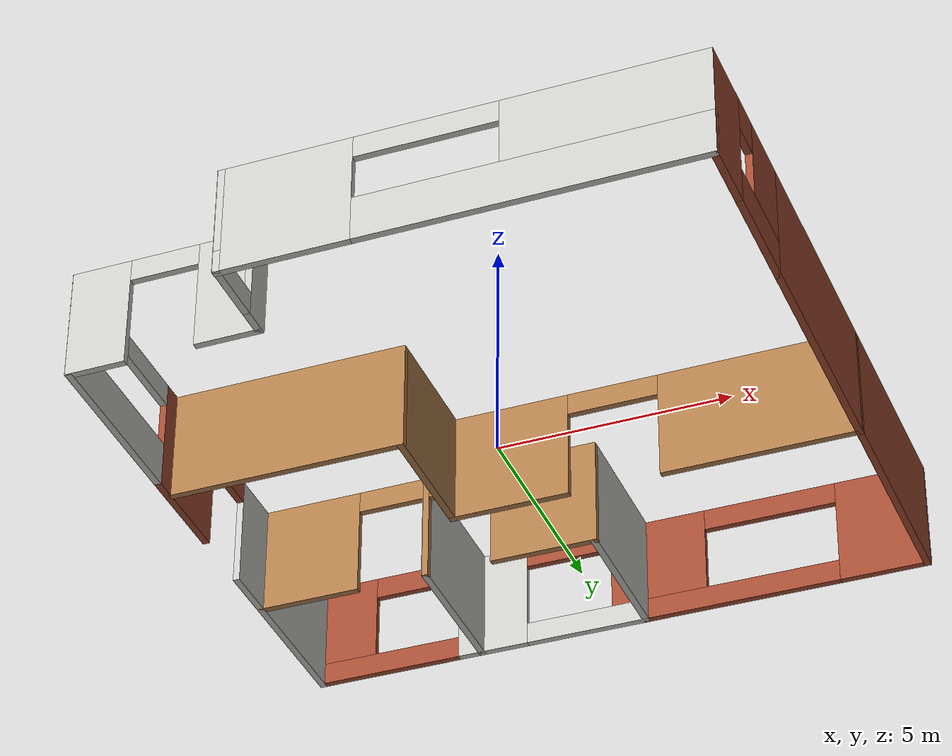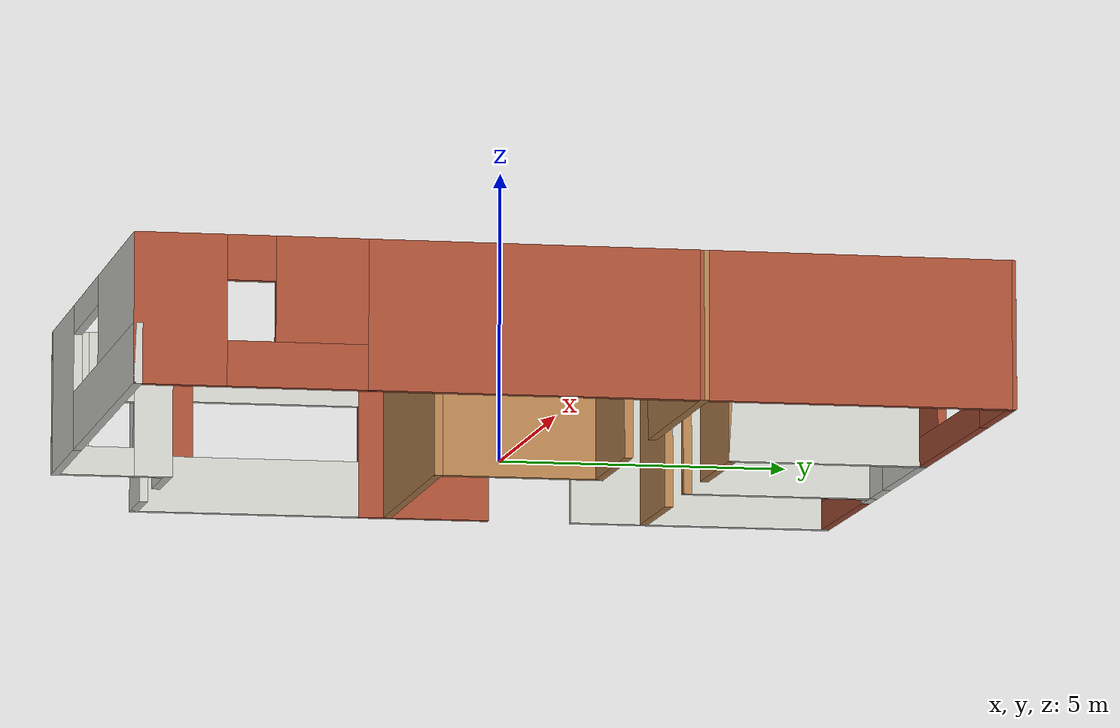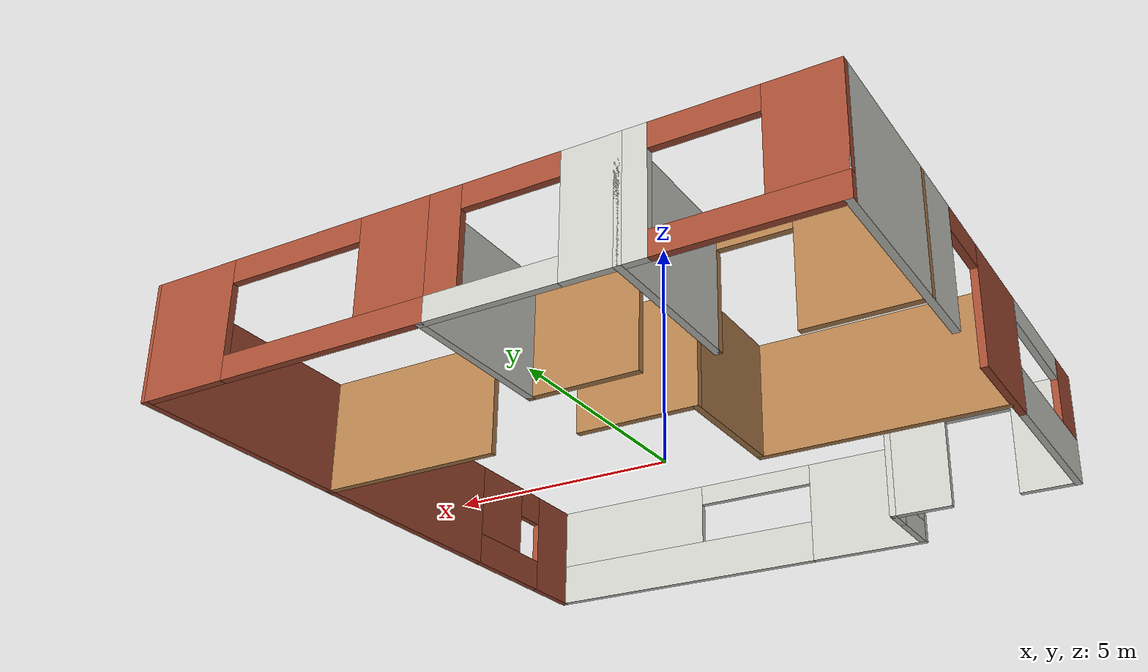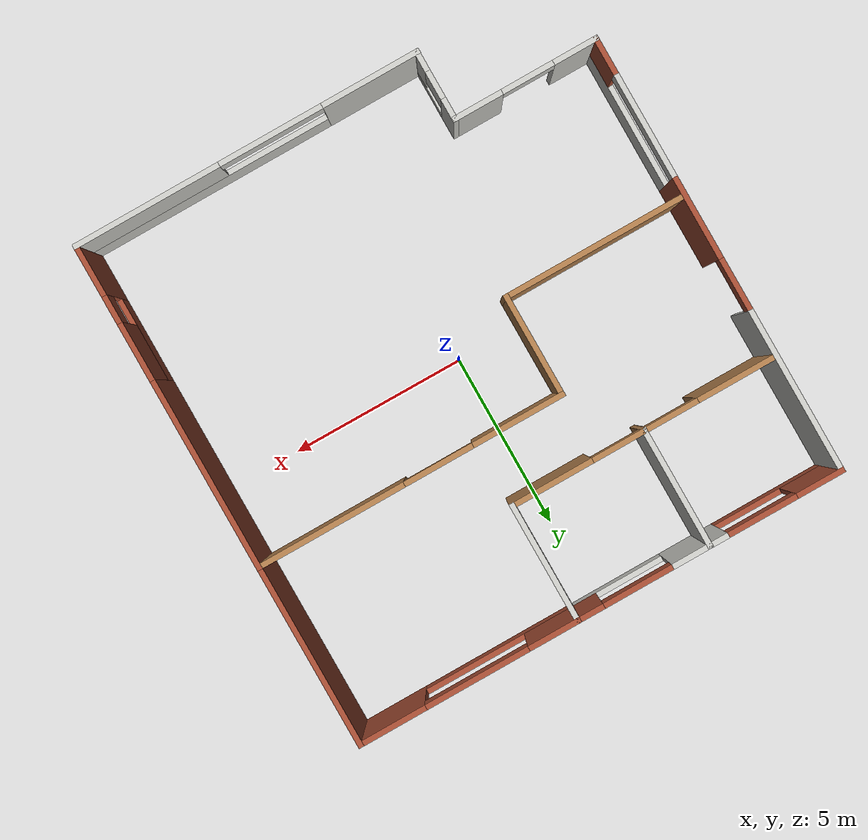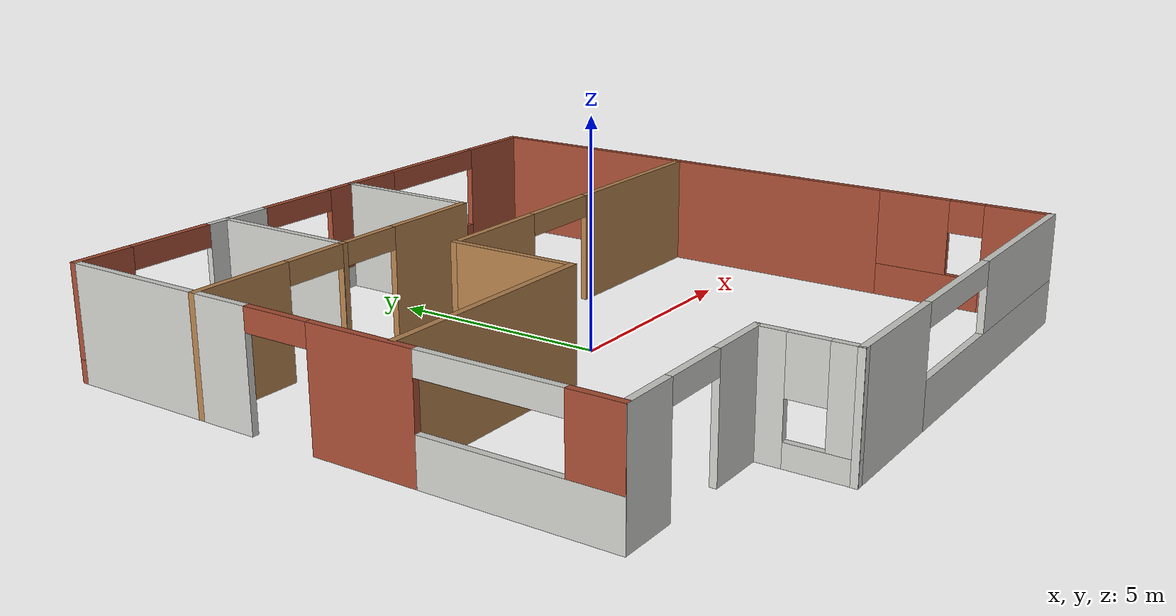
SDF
<?xml version='1.0'?>
<sdf version='1.6'>
  <model name='mybuilding_0_0'>
    <link name='Wall_100'>
      <pose frame=''>-4.97405 -5.32475 0 0 -0 0</pose>
      <inertial>
        <mass>1</mass>
        <pose frame=''>0 0 0 0 -0 0</pose>
        <inertia>
          <ixx>1</ixx>
          <ixy>0</ixy>
          <ixz>0</ixz>
          <iyy>1</iyy>
          <iyz>0</iyz>
          <izz>1</izz>
        </inertia>
      </inertial>
      <self_collide>0</self_collide>
      <kinematic>0</kinematic>
      <visual name='Wall_100_Visual_1'>
        <pose frame=''>1.40216 0 1.25 0 -0 0</pose>
        <geometry>
          <box>
            <size>1.44569 0.15 2.5</size>
          </box>
        </geometry>
        <material>
          <script>
            <uri>file://media/materials/scripts/gazebo.material</uri>
            <name>Gazebo/CeilingTiled</name>
          </script>
          <ambient>0.435 0.796 0.675 1</ambient>
          <diffuse>1 1 1 1</diffuse>
          <specular>0 0 0 1</specular>
          <emissive>0 0 0 1</emissive>
          <shader type='vertex'>
            <normal_map>__default__</normal_map>
          </shader>
        </material>
        <cast_shadows>1</cast_shadows>
        <transparency>0</transparency>
      </visual>
      <visual name='Wall_100_Visual_0'>
        <pose frame=''>-1.47284 0 1.25 0 -0 0</pose>
        <geometry>
          <box>
            <size>1.30431 0.15 2.5</size>
          </box>
        </geometry>
        <material>
          <script>
            <uri>file://media/materials/scripts/gazebo.material</uri>
            <name>Gazebo/CeilingTiled</name>
          </script>
          <ambient>0.435 0.796 0.675 1</ambient>
          <diffuse>1 1 1 1</diffuse>
          <specular>0 0 0 1</specular>
          <emissive>0 0 0 1</emissive>
          <shader type='vertex'>
            <normal_map>__default__</normal_map>
          </shader>
        </material>
        <cast_shadows>1</cast_shadows>
        <transparency>0</transparency>
      </visual>
      <visual name='Wall_100_Visual_2'>
        <pose frame=''>-0.07069 0 2.25 0 -0 0</pose>
        <geometry>
          <box>
            <size>1.5 0.15 0.5</size>
          </box>
        </geometry>
        <material>
          <script>
            <uri>file://media/materials/scripts/gazebo.material</uri>
            <name>Gazebo/CeilingTiled</name>
          </script>
          <ambient>0.435 0.796 0.675 1</ambient>
          <diffuse>1 1 1 1</diffuse>
          <specular>0 0 0 1</specular>
          <emissive>0 0 0 1</emissive>
          <shader type='vertex'>
            <normal_map>__default__</normal_map>
          </shader>
        </material>
        <cast_shadows>1</cast_shadows>
        <transparency>0</transparency>
      </visual>
      <collision name='Wall_100_Collision_0'>
        <laser_retro>0</laser_retro>
        <max_contacts>10</max_contacts>
        <pose frame=''>-1.47284 0 1.25 0 -0 0</pose>
        <geometry>
          <box>
            <size>1.30431 0.15 2.5</size>
          </box>
        </geometry>
        <surface>
          <friction>
            <ode>
              <mu>1</mu>
              <mu2>1</mu2>
              <fdir1>0 0 0</fdir1>
              <slip1>0</slip1>
              <slip2>0</slip2>
            </ode>
            <torsional>
              <coefficient>1</coefficient>
              <patch_radius>0</patch_radius>
              <surface_radius>0</surface_radius>
              <use_patch_radius>1</use_patch_radius>
              <ode>
                <slip>0</slip>
              </ode>
            </torsional>
          </friction>
          <bounce>
            <restitution_coefficient>0</restitution_coefficient>
            <threshold>1e+06</threshold>
          </bounce>
          <contact>
            <collide_without_contact>0</collide_without_contact>
            <collide_without_contact_bitmask>1</collide_without_contact_bitmask>
            <collide_bitmask>1</collide_bitmask>
            <ode>
              <soft_cfm>0</soft_cfm>
              <soft_erp>0.2</soft_erp>
              <kp>1e+13</kp>
              <kd>1</kd>
              <max_vel>0.01</max_vel>
              <min_depth>0</min_depth>
            </ode>
            <bullet>
              <split_impulse>1</split_impulse>
              <split_impulse_penetration_threshold>-0.01</split_impulse_penetration_threshold>
              <soft_cfm>0</soft_cfm>
              <soft_erp>0.2</soft_erp>
              <kp>1e+13</kp>
              <kd>1</kd>
            </bullet>
          </contact>
        </surface>
      </collision>
      <collision name='Wall_100_Collision_1'>
        <laser_retro>0</laser_retro>
        <max_contacts>10</max_contacts>
        <pose frame=''>1.40216 0 1.25 0 -0 0</pose>
        <geometry>
          <box>
            <size>1.44569 0.15 2.5</size>
          </box>
        </geometry>
        <surface>
          <friction>
            <ode>
              <mu>1</mu>
              <mu2>1</mu2>
              <fdir1>0 0 0</fdir1>
              <slip1>0</slip1>
              <slip2>0</slip2>
            </ode>
            <torsional>
              <coefficient>1</coefficient>
              <patch_radius>0</patch_radius>
              <surface_radius>0</surface_radius>
              <use_patch_radius>1</use_patch_radius>
              <ode>
                <slip>0</slip>
              </ode>
            </torsional>
          </friction>
          <bounce>
            <restitution_coefficient>0</restitution_coefficient>
            <threshold>1e+06</threshold>
          </bounce>
          <contact>
            <collide_without_contact>0</collide_without_contact>
            <collide_without_contact_bitmask>1</collide_without_contact_bitmask>
            <collide_bitmask>1</collide_bitmask>
            <ode>
              <soft_cfm>0</soft_cfm>
              <soft_erp>0.2</soft_erp>
              <kp>1e+13</kp>
              <kd>1</kd>
              <max_vel>0.01</max_vel>
              <min_depth>0</min_depth>
            </ode>
            <bullet>
              <split_impulse>1</split_impulse>
              <split_impulse_penetration_threshold>-0.01</split_impulse_penetration_threshold>
              <soft_cfm>0</soft_cfm>
              <soft_erp>0.2</soft_erp>
              <kp>1e+13</kp>
              <kd>1</kd>
            </bullet>
          </contact>
        </surface>
      </collision>
      <collision name='Wall_100_Collision_2'>
        <laser_retro>0</laser_retro>
        <max_contacts>10</max_contacts>
        <pose frame=''>-0.07069 0 2.25 0 -0 0</pose>
        <geometry>
          <box>
            <size>1.5 0.15 0.5</size>
          </box>
        </geometry>
        <surface>
          <friction>
            <ode>
              <mu>1</mu>
              <mu2>1</mu2>
              <fdir1>0 0 0</fdir1>
              <slip1>0</slip1>
              <slip2>0</slip2>
            </ode>
            <torsional>
              <coefficient>1</coefficient>
              <patch_radius>0</patch_radius>
              <surface_radius>0</surface_radius>
              <use_patch_radius>1</use_patch_radius>
              <ode>
                <slip>0</slip>
              </ode>
            </torsional>
          </friction>
          <bounce>
            <restitution_coefficient>0</restitution_coefficient>
            <threshold>1e+06</threshold>
          </bounce>
          <contact>
            <collide_without_contact>0</collide_without_contact>
            <collide_without_contact_bitmask>1</collide_without_contact_bitmask>
            <collide_bitmask>1</collide_bitmask>
            <ode>
              <soft_cfm>0</soft_cfm>
              <soft_erp>0.2</soft_erp>
              <kp>1e+13</kp>
              <kd>1</kd>
              <max_vel>0.01</max_vel>
              <min_depth>0</min_depth>
            </ode>
            <bullet>
              <split_impulse>1</split_impulse>
              <split_impulse_penetration_threshold>-0.01</split_impulse_penetration_threshold>
              <soft_cfm>0</soft_cfm>
              <soft_erp>0.2</soft_erp>
              <kp>1e+13</kp>
              <kd>1</kd>
            </bullet>
          </contact>
        </surface>
      </collision>
    </link>
    <link name='Wall_102'>
      <pose frame=''>-2.91535 -6.30192 0 0 0 -1.5708</pose>
      <inertial>
        <mass>1</mass>
        <pose frame=''>0 0 0 0 -0 0</pose>
        <inertia>
          <ixx>1</ixx>
          <ixy>0</ixy>
          <ixz>0</ixz>
          <iyy>1</iyy>
          <iyz>0</iyz>
          <izz>1</izz>
        </inertia>
      </inertial>
      <self_collide>0</self_collide>
      <kinematic>0</kinematic>
      <visual name='Wall_102_Visual_0'>
        <pose frame=''>-0.715877 0 1.25 0 -0 0</pose>
        <geometry>
          <box>
            <size>0.672904 0.15 2.5</size>
          </box>
        </geometry>
        <material>
          <script>
            <uri>file://media/materials/scripts/gazebo.material</uri>
            <name>Gazebo/CeilingTiled</name>
          </script>
          <ambient>1 0.765 0.306 1</ambient>
          <diffuse>1 1 1 1</diffuse>
          <specular>0 0 0 1</specular>
          <emissive>0 0 0 1</emissive>
          <shader type='vertex'>
            <normal_map>__default__</normal_map>
          </shader>
        </material>
        <cast_shadows>1</cast_shadows>
        <transparency>0</transparency>
      </visual>
      <visual name='Wall_102_Visual_1'>
        <pose frame=''>0.336452 0 0.25 0 -0 0</pose>
        <geometry>
          <box>
            <size>1.43175 0.15 0.5</size>
          </box>
        </geometry>
        <material>
          <script>
            <uri>file://media/materials/scripts/gazebo.material</uri>
            <name>Gazebo/CeilingTiled</name>
          </script>
          <ambient>1 0.765 0.306 1</ambient>
          <diffuse>1 1 1 1</diffuse>
          <specular>0 0 0 1</specular>
          <emissive>0 0 0 1</emissive>
          <shader type='vertex'>
            <normal_map>__default__</normal_map>
          </shader>
        </material>
        <cast_shadows>1</cast_shadows>
        <transparency>0</transparency>
      </visual>
      <visual name='Wall_102_Visual_3'>
        <pose frame=''>0.020576 0 1.9 0 -0 0</pose>
        <geometry>
          <box>
            <size>0.8 0.15 1.2</size>
          </box>
        </geometry>
        <material>
          <script>
            <uri>file://media/materials/scripts/gazebo.material</uri>
            <name>Gazebo/CeilingTiled</name>
          </script>
          <ambient>1 0.765 0.306 1</ambient>
          <diffuse>1 1 1 1</diffuse>
          <specular>0 0 0 1</specular>
          <emissive>0 0 0 1</emissive>
          <shader type='vertex'>
            <normal_map>__default__</normal_map>
          </shader>
        </material>
        <cast_shadows>1</cast_shadows>
        <transparency>0</transparency>
      </visual>
      <visual name='Wall_102_Visual_2'>
        <pose frame=''>0.736452 0 1.5 0 -0 0</pose>
        <geometry>
          <box>
            <size>0.631753 0.15 2</size>
          </box>
        </geometry>
        <material>
          <script>
            <uri>file://media/materials/scripts/gazebo.material</uri>
            <name>Gazebo/CeilingTiled</name>
          </script>
          <ambient>1 0.765 0.306 1</ambient>
          <diffuse>1 1 1 1</diffuse>
          <specular>0 0 0 1</specular>
          <emissive>0 0 0 1</emissive>
          <shader type='vertex'>
            <normal_map>__default__</normal_map>
          </shader>
        </material>
        <cast_shadows>1</cast_shadows>
        <transparency>0</transparency>
      </visual>
      <collision name='Wall_102_Collision_3'>
        <laser_retro>0</laser_retro>
        <max_contacts>10</max_contacts>
        <pose frame=''>0.020576 0 1.9 0 -0 0</pose>
        <geometry>
          <box>
            <size>0.8 0.15 1.2</size>
          </box>
        </geometry>
        <surface>
          <friction>
            <ode>
              <mu>1</mu>
              <mu2>1</mu2>
              <fdir1>0 0 0</fdir1>
              <slip1>0</slip1>
              <slip2>0</slip2>
            </ode>
            <torsional>
              <coefficient>1</coefficient>
              <patch_radius>0</patch_radius>
              <surface_radius>0</surface_radius>
              <use_patch_radius>1</use_patch_radius>
              <ode>
                <slip>0</slip>
              </ode>
            </torsional>
          </friction>
          <bounce>
            <restitution_coefficient>0</restitution_coefficient>
            <threshold>1e+06</threshold>
          </bounce>
          <contact>
            <collide_without_contact>0</collide_without_contact>
            <collide_without_contact_bitmask>1</collide_without_contact_bitmask>
            <collide_bitmask>1</collide_bitmask>
            <ode>
              <soft_cfm>0</soft_cfm>
              <soft_erp>0.2</soft_erp>
              <kp>1e+13</kp>
              <kd>1</kd>
              <max_vel>0.01</max_vel>
              <min_depth>0</min_depth>
            </ode>
            <bullet>
              <split_impulse>1</split_impulse>
              <split_impulse_penetration_threshold>-0.01</split_impulse_penetration_threshold>
              <soft_cfm>0</soft_cfm>
              <soft_erp>0.2</soft_erp>
              <kp>1e+13</kp>
              <kd>1</kd>
            </bullet>
          </contact>
        </surface>
      </collision>
      <collision name='Wall_102_Collision_0'>
        <laser_retro>0</laser_retro>
        <max_contacts>10</max_contacts>
        <pose frame=''>-0.715877 0 1.25 0 -0 0</pose>
        <geometry>
          <box>
            <size>0.672904 0.15 2.5</size>
          </box>
        </geometry>
        <surface>
          <friction>
            <ode>
              <mu>1</mu>
              <mu2>1</mu2>
              <fdir1>0 0 0</fdir1>
              <slip1>0</slip1>
              <slip2>0</slip2>
            </ode>
            <torsional>
              <coefficient>1</coefficient>
              <patch_radius>0</patch_radius>
              <surface_radius>0</surface_radius>
              <use_patch_radius>1</use_patch_radius>
              <ode>
                <slip>0</slip>
              </ode>
            </torsional>
          </friction>
          <bounce>
            <restitution_coefficient>0</restitution_coefficient>
            <threshold>1e+06</threshold>
          </bounce>
          <contact>
            <collide_without_contact>0</collide_without_contact>
            <collide_without_contact_bitmask>1</collide_without_contact_bitmask>
            <collide_bitmask>1</collide_bitmask>
            <ode>
              <soft_cfm>0</soft_cfm>
              <soft_erp>0.2</soft_erp>
              <kp>1e+13</kp>
              <kd>1</kd>
              <max_vel>0.01</max_vel>
              <min_depth>0</min_depth>
            </ode>
            <bullet>
              <split_impulse>1</split_impulse>
              <split_impulse_penetration_threshold>-0.01</split_impulse_penetration_threshold>
              <soft_cfm>0</soft_cfm>
              <soft_erp>0.2</soft_erp>
              <kp>1e+13</kp>
              <kd>1</kd>
            </bullet>
          </contact>
        </surface>
      </collision>
      <collision name='Wall_102_Collision_1'>
        <laser_retro>0</laser_retro>
        <max_contacts>10</max_contacts>
        <pose frame=''>0.336452 0 0.25 0 -0 0</pose>
        <geometry>
          <box>
            <size>1.43175 0.15 0.5</size>
          </box>
        </geometry>
        <surface>
          <friction>
            <ode>
              <mu>1</mu>
              <mu2>1</mu2>
              <fdir1>0 0 0</fdir1>
              <slip1>0</slip1>
              <slip2>0</slip2>
            </ode>
            <torsional>
              <coefficient>1</coefficient>
              <patch_radius>0</patch_radius>
              <surface_radius>0</surface_radius>
              <use_patch_radius>1</use_patch_radius>
              <ode>
                <slip>0</slip>
              </ode>
            </torsional>
          </friction>
          <bounce>
            <restitution_coefficient>0</restitution_coefficient>
            <threshold>1e+06</threshold>
          </bounce>
          <contact>
            <collide_without_contact>0</collide_without_contact>
            <collide_without_contact_bitmask>1</collide_without_contact_bitmask>
            <collide_bitmask>1</collide_bitmask>
            <ode>
              <soft_cfm>0</soft_cfm>
              <soft_erp>0.2</soft_erp>
              <kp>1e+13</kp>
              <kd>1</kd>
              <max_vel>0.01</max_vel>
              <min_depth>0</min_depth>
            </ode>
            <bullet>
              <split_impulse>1</split_impulse>
              <split_impulse_penetration_threshold>-0.01</split_impulse_penetration_threshold>
              <soft_cfm>0</soft_cfm>
              <soft_erp>0.2</soft_erp>
              <kp>1e+13</kp>
              <kd>1</kd>
            </bullet>
          </contact>
        </surface>
      </collision>
      <collision name='Wall_102_Collision_2'>
        <laser_retro>0</laser_retro>
        <max_contacts>10</max_contacts>
        <pose frame=''>0.736452 0 1.5 0 -0 0</pose>
        <geometry>
          <box>
            <size>0.631753 0.15 2</size>
          </box>
        </geometry>
        <surface>
          <friction>
            <ode>
              <mu>1</mu>
              <mu2>1</mu2>
              <fdir1>0 0 0</fdir1>
              <slip1>0</slip1>
              <slip2>0</slip2>
            </ode>
            <torsional>
              <coefficient>1</coefficient>
              <patch_radius>0</patch_radius>
              <surface_radius>0</surface_radius>
              <use_patch_radius>1</use_patch_radius>
              <ode>
                <slip>0</slip>
              </ode>
            </torsional>
          </friction>
          <bounce>
            <restitution_coefficient>0</restitution_coefficient>
            <threshold>1e+06</threshold>
          </bounce>
          <contact>
            <collide_without_contact>0</collide_without_contact>
            <collide_without_contact_bitmask>1</collide_without_contact_bitmask>
            <collide_bitmask>1</collide_bitmask>
            <ode>
              <soft_cfm>0</soft_cfm>
              <soft_erp>0.2</soft_erp>
              <kp>1e+13</kp>
              <kd>1</kd>
              <max_vel>0.01</max_vel>
              <min_depth>0</min_depth>
            </ode>
            <bullet>
              <split_impulse>1</split_impulse>
              <split_impulse_penetration_threshold>-0.01</split_impulse_penetration_threshold>
              <soft_cfm>0</soft_cfm>
              <soft_erp>0.2</soft_erp>
              <kp>1e+13</kp>
              <kd>1</kd>
            </bullet>
          </contact>
        </surface>
      </collision>
    </link>
    <link name='Wall_104'>
      <pose frame=''>2.05282 -7.27925 0 0 0 -3.1e-05</pose>
      <self_collide>0</self_collide>
      <kinematic>0</kinematic>
      <visual name='Wall_104_Visual_0'>
        <pose frame=''>-3.62649 0 1.25 0 -0 0</pose>
        <geometry>
          <box>
            <size>2.85075 0.15 2.5</size>
          </box>
        </geometry>
        <material>
          <script>
            <uri>file://media/materials/scripts/gazebo.material</uri>
            <name>Gazebo/CeilingTiled</name>
          </script>
          <ambient>0.435294 0.796078 0.67451 1</ambient>
          <diffuse>1 1 1 1</diffuse>
          <specular>0 0 0 1</specular>
          <emissive>0 0 0 1</emissive>
        </material>
        <cast_shadows>1</cast_shadows>
        <transparency>0</transparency>
      </visual>
      <visual name='Wall_104_Visual_2'>
        <pose frame=''>2.92537 0 1.75 0 -0 0</pose>
        <geometry>
          <box>
            <size>4.25299 0.15 1.5</size>
          </box>
        </geometry>
        <material>
          <script>
            <uri>file://media/materials/scripts/gazebo.material</uri>
            <name>Gazebo/CeilingTiled</name>
          </script>
          <ambient>0.435294 0.796078 0.67451 1</ambient>
          <diffuse>1 1 1 1</diffuse>
          <specular>0 0 0 1</specular>
          <emissive>0 0 0 1</emissive>
        </material>
        <cast_shadows>1</cast_shadows>
        <transparency>0</transparency>
      </visual>
      <visual name='Wall_104_Visual_1'>
        <pose frame=''>1.42538 0 0.5 0 -0 0</pose>
        <geometry>
          <box>
            <size>7.25299 0.15 1</size>
          </box>
        </geometry>
        <material>
          <script>
            <uri>file://media/materials/scripts/gazebo.material</uri>
            <name>Gazebo/CeilingTiled</name>
          </script>
          <ambient>0.435294 0.796078 0.67451 1</ambient>
          <diffuse>1 1 1 1</diffuse>
          <specular>0 0 0 1</specular>
          <emissive>0 0 0 1</emissive>
        </material>
        <cast_shadows>1</cast_shadows>
        <transparency>0</transparency>
      </visual>
      <visual name='Wall_104_Visual_3'>
        <pose frame=''>-0.70112 0 2.25 0 -0 0</pose>
        <geometry>
          <box>
            <size>3 0.15 0.5</size>
          </box>
        </geometry>
        <material>
          <script>
            <uri>file://media/materials/scripts/gazebo.material</uri>
            <name>Gazebo/CeilingTiled</name>
          </script>
          <ambient>0.435294 0.796078 0.67451 1</ambient>
          <diffuse>1 1 1 1</diffuse>
          <specular>0 0 0 1</specular>
          <emissive>0 0 0 1</emissive>
        </material>
        <cast_shadows>1</cast_shadows>
        <transparency>0</transparency>
      </visual>
      <collision name='Wall_104_Collision_0'>
        <laser_retro>0</laser_retro>
        <max_contacts>10</max_contacts>
        <pose frame=''>-3.62649 0 1.25 0 -0 0</pose>
        <geometry>
          <box>
            <size>2.85075 0.15 2.5</size>
          </box>
        </geometry>
        <surface>
          <friction>
            <ode>
              <mu>1</mu>
              <mu2>1</mu2>
              <fdir1>0 0 0</fdir1>
              <slip1>0</slip1>
              <slip2>0</slip2>
            </ode>
            <torsional>
              <coefficient>1</coefficient>
              <patch_radius>0</patch_radius>
              <surface_radius>0</surface_radius>
              <use_patch_radius>1</use_patch_radius>
              <ode>
                <slip>0</slip>
              </ode>
            </torsional>
          </friction>
          <bounce>
            <restitution_coefficient>0</restitution_coefficient>
            <threshold>1e+06</threshold>
          </bounce>
          <contact>
            <collide_without_contact>0</collide_without_contact>
            <collide_without_contact_bitmask>1</collide_without_contact_bitmask>
            <collide_bitmask>1</collide_bitmask>
            <ode>
              <soft_cfm>0</soft_cfm>
              <soft_erp>0.2</soft_erp>
              <kp>1e+13</kp>
              <kd>1</kd>
              <max_vel>0.01</max_vel>
              <min_depth>0</min_depth>
            </ode>
            <bullet>
              <split_impulse>1</split_impulse>
              <split_impulse_penetration_threshold>-0.01</split_impulse_penetration_threshold>
              <soft_cfm>0</soft_cfm>
              <soft_erp>0.2</soft_erp>
              <kp>1e+13</kp>
              <kd>1</kd>
            </bullet>
          </contact>
        </surface>
      </collision>
      <collision name='Wall_104_Collision_2'>
        <laser_retro>0</laser_retro>
        <max_contacts>10</max_contacts>
        <pose frame=''>2.92537 0 1.75 0 -0 0</pose>
        <geometry>
          <box>
            <size>4.25299 0.15 1.5</size>
          </box>
        </geometry>
        <surface>
          <friction>
            <ode>
              <mu>1</mu>
              <mu2>1</mu2>
              <fdir1>0 0 0</fdir1>
              <slip1>0</slip1>
              <slip2>0</slip2>
            </ode>
            <torsional>
              <coefficient>1</coefficient>
              <patch_radius>0</patch_radius>
              <surface_radius>0</surface_radius>
              <use_patch_radius>1</use_patch_radius>
              <ode>
                <slip>0</slip>
              </ode>
            </torsional>
          </friction>
          <bounce>
            <restitution_coefficient>0</restitution_coefficient>
            <threshold>1e+06</threshold>
          </bounce>
          <contact>
            <collide_without_contact>0</collide_without_contact>
            <collide_without_contact_bitmask>1</collide_without_contact_bitmask>
            <collide_bitmask>1</collide_bitmask>
            <ode>
              <soft_cfm>0</soft_cfm>
              <soft_erp>0.2</soft_erp>
              <kp>1e+13</kp>
              <kd>1</kd>
              <max_vel>0.01</max_vel>
              <min_depth>0</min_depth>
            </ode>
            <bullet>
              <split_impulse>1</split_impulse>
              <split_impulse_penetration_threshold>-0.01</split_impulse_penetration_threshold>
              <soft_cfm>0</soft_cfm>
              <soft_erp>0.2</soft_erp>
              <kp>1e+13</kp>
              <kd>1</kd>
            </bullet>
          </contact>
        </surface>
      </collision>
      <collision name='Wall_104_Collision_1'>
        <laser_retro>0</laser_retro>
        <max_contacts>10</max_contacts>
        <pose frame=''>1.42538 0 0.5 0 -0 0</pose>
        <geometry>
          <box>
            <size>7.25299 0.15 1</size>
          </box>
        </geometry>
        <surface>
          <friction>
            <ode>
              <mu>1</mu>
              <mu2>1</mu2>
              <fdir1>0 0 0</fdir1>
              <slip1>0</slip1>
              <slip2>0</slip2>
            </ode>
            <torsional>
              <coefficient>1</coefficient>
              <patch_radius>0</patch_radius>
              <surface_radius>0</surface_radius>
              <use_patch_radius>1</use_patch_radius>
              <ode>
                <slip>0</slip>
              </ode>
            </torsional>
          </friction>
          <bounce>
            <restitution_coefficient>0</restitution_coefficient>
            <threshold>1e+06</threshold>
          </bounce>
          <contact>
            <collide_without_contact>0</collide_without_contact>
            <collide_without_contact_bitmask>1</collide_without_contact_bitmask>
            <collide_bitmask>1</collide_bitmask>
            <ode>
              <soft_cfm>0</soft_cfm>
              <soft_erp>0.2</soft_erp>
              <kp>1e+13</kp>
              <kd>1</kd>
              <max_vel>0.01</max_vel>
              <min_depth>0</min_depth>
            </ode>
            <bullet>
              <split_impulse>1</split_impulse>
              <split_impulse_penetration_threshold>-0.01</split_impulse_penetration_threshold>
              <soft_cfm>0</soft_cfm>
              <soft_erp>0.2</soft_erp>
              <kp>1e+13</kp>
              <kd>1</kd>
            </bullet>
          </contact>
        </surface>
      </collision>
      <collision name='Wall_104_Collision_3'>
        <laser_retro>0</laser_retro>
        <max_contacts>10</max_contacts>
        <pose frame=''>-0.70112 0 2.25 0 -0 0</pose>
        <geometry>
          <box>
            <size>3 0.15 0.5</size>
          </box>
        </geometry>
        <surface>
          <friction>
            <ode>
              <mu>1</mu>
              <mu2>1</mu2>
              <fdir1>0 0 0</fdir1>
              <slip1>0</slip1>
              <slip2>0</slip2>
            </ode>
            <torsional>
              <coefficient>1</coefficient>
              <patch_radius>0</patch_radius>
              <surface_radius>0</surface_radius>
              <use_patch_radius>1</use_patch_radius>
              <ode>
                <slip>0</slip>
              </ode>
            </torsional>
          </friction>
          <bounce>
            <restitution_coefficient>0</restitution_coefficient>
            <threshold>1e+06</threshold>
          </bounce>
          <contact>
            <collide_without_contact>0</collide_without_contact>
            <collide_without_contact_bitmask>1</collide_without_contact_bitmask>
            <collide_bitmask>1</collide_bitmask>
            <ode>
              <soft_cfm>0</soft_cfm>
              <soft_erp>0.2</soft_erp>
              <kp>1e+13</kp>
              <kd>1</kd>
              <max_vel>0.01</max_vel>
              <min_depth>0</min_depth>
            </ode>
            <bullet>
              <split_impulse>1</split_impulse>
              <split_impulse_penetration_threshold>-0.01</split_impulse_penetration_threshold>
              <soft_cfm>0</soft_cfm>
              <soft_erp>0.2</soft_erp>
              <kp>1e+13</kp>
              <kd>1</kd>
            </bullet>
          </contact>
        </surface>
      </collision>
    </link>
    <link name='Wall_106'>
      <pose frame=''>7.02969 -5.3499 0 0 -0 1.5708</pose>
      <self_collide>0</self_collide>
      <kinematic>0</kinematic>
      <visual name='Wall_106_Visual_0'>
        <pose frame=''>-1.23742 0 1.25 0 -0 0</pose>
        <geometry>
          <box>
            <size>1.53383 0.15 2.5</size>
          </box>
        </geometry>
        <material>
          <script>
            <uri>file://media/materials/scripts/gazebo.material</uri>
            <name>Gazebo/Bricks</name>
          </script>
          <ambient>1 1 1 1</ambient>
          <diffuse>1 1 1 1</diffuse>
          <specular>0.2 0.2 0.2 1</specular>
          <emissive>0 0 0 1</emissive>
        </material>
        <cast_shadows>1</cast_shadows>
        <transparency>0</transparency>
      </visual>
      <visual name='Wall_106_Visual_1'>
        <pose frame=''>0.766915 0 0.375 0 -0 0</pose>
        <geometry>
          <box>
            <size>2.47484 0.15 0.75</size>
          </box>
        </geometry>
        <material>
          <script>
            <uri>file://media/materials/scripts/gazebo.material</uri>
            <name>Gazebo/Bricks</name>
          </script>
          <ambient>1 1 1 1</ambient>
          <diffuse>1 1 1 1</diffuse>
          <specular>0.2 0.2 0.2 1</specular>
          <emissive>0 0 0 1</emissive>
        </material>
        <cast_shadows>1</cast_shadows>
        <transparency>0</transparency>
      </visual>
      <visual name='Wall_106_Visual_2'>
        <pose frame=''>1.16691 0 1.625 0 -0 0</pose>
        <geometry>
          <box>
            <size>1.67484 0.15 1.75</size>
          </box>
        </geometry>
        <material>
          <script>
            <uri>file://media/materials/scripts/gazebo.material</uri>
            <name>Gazebo/Bricks</name>
          </script>
          <ambient>1 1 1 1</ambient>
          <diffuse>1 1 1 1</diffuse>
          <specular>0.2 0.2 0.2 1</specular>
          <emissive>0 0 0 1</emissive>
        </material>
        <cast_shadows>1</cast_shadows>
        <transparency>0</transparency>
      </visual>
      <visual name='Wall_106_Visual_3'>
        <pose frame=''>-0.070504 0 2.125 0 -0 0</pose>
        <geometry>
          <box>
            <size>0.8 0.15 0.75</size>
          </box>
        </geometry>
        <material>
          <script>
            <uri>file://media/materials/scripts/gazebo.material</uri>
            <name>Gazebo/Bricks</name>
          </script>
          <ambient>1 1 1 1</ambient>
          <diffuse>1 1 1 1</diffuse>
          <specular>0.2 0.2 0.2 1</specular>
          <emissive>0 0 0 1</emissive>
        </material>
        <cast_shadows>1</cast_shadows>
        <transparency>0</transparency>
      </visual>
      <collision name='Wall_106_Collision_0'>
        <laser_retro>0</laser_retro>
        <max_contacts>10</max_contacts>
        <pose frame=''>-1.23742 0 1.25 0 -0 0</pose>
        <geometry>
          <box>
            <size>1.53383 0.15 2.5</size>
          </box>
        </geometry>
        <surface>
          <friction>
            <ode>
              <mu>1</mu>
              <mu2>1</mu2>
              <fdir1>0 0 0</fdir1>
              <slip1>0</slip1>
              <slip2>0</slip2>
            </ode>
            <torsional>
              <coefficient>1</coefficient>
              <patch_radius>0</patch_radius>
              <surface_radius>0</surface_radius>
              <use_patch_radius>1</use_patch_radius>
              <ode>
                <slip>0</slip>
              </ode>
            </torsional>
          </friction>
          <bounce>
            <restitution_coefficient>0</restitution_coefficient>
            <threshold>1e+06</threshold>
          </bounce>
          <contact>
            <collide_without_contact>0</collide_without_contact>
            <collide_without_contact_bitmask>1</collide_without_contact_bitmask>
            <collide_bitmask>1</collide_bitmask>
            <ode>
              <soft_cfm>0</soft_cfm>
              <soft_erp>0.2</soft_erp>
              <kp>1e+13</kp>
              <kd>1</kd>
              <max_vel>0.01</max_vel>
              <min_depth>0</min_depth>
            </ode>
            <bullet>
              <split_impulse>1</split_impulse>
              <split_impulse_penetration_threshold>-0.01</split_impulse_penetration_threshold>
              <soft_cfm>0</soft_cfm>
              <soft_erp>0.2</soft_erp>
              <kp>1e+13</kp>
              <kd>1</kd>
            </bullet>
          </contact>
        </surface>
      </collision>
      <collision name='Wall_106_Collision_2'>
        <laser_retro>0</laser_retro>
        <max_contacts>10</max_contacts>
        <pose frame=''>1.16691 0 1.625 0 -0 0</pose>
        <geometry>
          <box>
            <size>1.67484 0.15 1.75</size>
          </box>
        </geometry>
        <surface>
          <friction>
            <ode>
              <mu>1</mu>
              <mu2>1</mu2>
              <fdir1>0 0 0</fdir1>
              <slip1>0</slip1>
              <slip2>0</slip2>
            </ode>
            <torsional>
              <coefficient>1</coefficient>
              <patch_radius>0</patch_radius>
              <surface_radius>0</surface_radius>
              <use_patch_radius>1</use_patch_radius>
              <ode>
                <slip>0</slip>
              </ode>
            </torsional>
          </friction>
          <bounce>
            <restitution_coefficient>0</restitution_coefficient>
            <threshold>1e+06</threshold>
          </bounce>
          <contact>
            <collide_without_contact>0</collide_without_contact>
            <collide_without_contact_bitmask>1</collide_without_contact_bitmask>
            <collide_bitmask>1</collide_bitmask>
            <ode>
              <soft_cfm>0</soft_cfm>
              <soft_erp>0.2</soft_erp>
              <kp>1e+13</kp>
              <kd>1</kd>
              <max_vel>0.01</max_vel>
              <min_depth>0</min_depth>
            </ode>
            <bullet>
              <split_impulse>1</split_impulse>
              <split_impulse_penetration_threshold>-0.01</split_impulse_penetration_threshold>
              <soft_cfm>0</soft_cfm>
              <soft_erp>0.2</soft_erp>
              <kp>1e+13</kp>
              <kd>1</kd>
            </bullet>
          </contact>
        </surface>
      </collision>
      <collision name='Wall_106_Collision_1'>
        <laser_retro>0</laser_retro>
        <max_contacts>10</max_contacts>
        <pose frame=''>0.766915 0 0.375 0 -0 0</pose>
        <geometry>
          <box>
            <size>2.47484 0.15 0.75</size>
          </box>
        </geometry>
        <surface>
          <friction>
            <ode>
              <mu>1</mu>
              <mu2>1</mu2>
              <fdir1>0 0 0</fdir1>
              <slip1>0</slip1>
              <slip2>0</slip2>
            </ode>
            <torsional>
              <coefficient>1</coefficient>
              <patch_radius>0</patch_radius>
              <surface_radius>0</surface_radius>
              <use_patch_radius>1</use_patch_radius>
              <ode>
                <slip>0</slip>
              </ode>
            </torsional>
          </friction>
          <bounce>
            <restitution_coefficient>0</restitution_coefficient>
            <threshold>1e+06</threshold>
          </bounce>
          <contact>
            <collide_without_contact>0</collide_without_contact>
            <collide_without_contact_bitmask>1</collide_without_contact_bitmask>
            <collide_bitmask>1</collide_bitmask>
            <ode>
              <soft_cfm>0</soft_cfm>
              <soft_erp>0.2</soft_erp>
              <kp>1e+13</kp>
              <kd>1</kd>
              <max_vel>0.01</max_vel>
              <min_depth>0</min_depth>
            </ode>
            <bullet>
              <split_impulse>1</split_impulse>
              <split_impulse_penetration_threshold>-0.01</split_impulse_penetration_threshold>
              <soft_cfm>0</soft_cfm>
              <soft_erp>0.2</soft_erp>
              <kp>1e+13</kp>
              <kd>1</kd>
            </bullet>
          </contact>
        </surface>
      </collision>
      <collision name='Wall_106_Collision_3'>
        <laser_retro>0</laser_retro>
        <max_contacts>10</max_contacts>
        <pose frame=''>-0.070504 0 2.125 0 -0 0</pose>
        <geometry>
          <box>
            <size>0.8 0.15 0.75</size>
          </box>
        </geometry>
        <surface>
          <friction>
            <ode>
              <mu>1</mu>
              <mu2>1</mu2>
              <fdir1>0 0 0</fdir1>
              <slip1>0</slip1>
              <slip2>0</slip2>
            </ode>
            <torsional>
              <coefficient>1</coefficient>
              <patch_radius>0</patch_radius>
              <surface_radius>0</surface_radius>
              <use_patch_radius>1</use_patch_radius>
              <ode>
                <slip>0</slip>
              </ode>
            </torsional>
          </friction>
          <bounce>
            <restitution_coefficient>0</restitution_coefficient>
            <threshold>1e+06</threshold>
          </bounce>
          <contact>
            <collide_without_contact>0</collide_without_contact>
            <collide_without_contact_bitmask>1</collide_without_contact_bitmask>
            <collide_bitmask>1</collide_bitmask>
            <ode>
              <soft_cfm>0</soft_cfm>
              <soft_erp>0.2</soft_erp>
              <kp>1e+13</kp>
              <kd>1</kd>
              <max_vel>0.01</max_vel>
              <min_depth>0</min_depth>
            </ode>
            <bullet>
              <split_impulse>1</split_impulse>
              <split_impulse_penetration_threshold>-0.01</split_impulse_penetration_threshold>
              <soft_cfm>0</soft_cfm>
              <soft_erp>0.2</soft_erp>
              <kp>1e+13</kp>
              <kd>1</kd>
            </bullet>
          </contact>
        </surface>
      </collision>
    </link>
    <link name='Wall_110'>
      <pose frame=''>7.02969 -0.662398 0 0 -0 1.5708</pose>
      <self_collide>0</self_collide>
      <kinematic>0</kinematic>
      <visual name='Wall_110_Visual'>
        <pose frame=''>0 0 1.25 0 -0 0</pose>
        <geometry>
          <box>
            <size>5.666 0.15 2.5</size>
          </box>
        </geometry>
        <material>
          <script>
            <uri>file://media/materials/scripts/gazebo.material</uri>
            <name>Gazebo/Bricks</name>
          </script>
          <ambient>1 1 1 1</ambient>
          <diffuse>1 1 1 1</diffuse>
          <specular>0.2 0.2 0.2 1</specular>
          <emissive>0 0 0 1</emissive>
        </material>
        <cast_shadows>1</cast_shadows>
        <transparency>0</transparency>
      </visual>
      <collision name='Wall_110_Collision'>
        <laser_retro>0</laser_retro>
        <max_contacts>10</max_contacts>
        <pose frame=''>0 0 1.25 0 -0 0</pose>
        <geometry>
          <box>
            <size>5.666 0.15 2.5</size>
          </box>
        </geometry>
        <surface>
          <friction>
            <ode>
              <mu>1</mu>
              <mu2>1</mu2>
              <fdir1>0 0 0</fdir1>
              <slip1>0</slip1>
              <slip2>0</slip2>
            </ode>
            <torsional>
              <coefficient>1</coefficient>
              <patch_radius>0</patch_radius>
              <surface_radius>0</surface_radius>
              <use_patch_radius>1</use_patch_radius>
              <ode>
                <slip>0</slip>
              </ode>
            </torsional>
          </friction>
          <bounce>
            <restitution_coefficient>0</restitution_coefficient>
            <threshold>1e+06</threshold>
          </bounce>
          <contact>
            <collide_without_contact>0</collide_without_contact>
            <collide_without_contact_bitmask>1</collide_without_contact_bitmask>
            <collide_bitmask>1</collide_bitmask>
            <ode>
              <soft_cfm>0</soft_cfm>
              <soft_erp>0.2</soft_erp>
              <kp>1e+13</kp>
              <kd>1</kd>
              <max_vel>0.01</max_vel>
              <min_depth>0</min_depth>
            </ode>
            <bullet>
              <split_impulse>1</split_impulse>
              <split_impulse_penetration_threshold>-0.01</split_impulse_penetration_threshold>
              <soft_cfm>0</soft_cfm>
              <soft_erp>0.2</soft_erp>
              <kp>1e+13</kp>
              <kd>1</kd>
            </bullet>
          </contact>
        </surface>
      </collision>
    </link>
    <link name='Wall_112'>
      <pose frame=''>2.60469 2.0956 0 0 -0 3.14159</pose>
      <self_collide>0</self_collide>
      <kinematic>0</kinematic>
      <visual name='Wall_112_Visual_0'>
        <pose frame=''>-2.34058 0 1.25 0 -0 0</pose>
        <geometry>
          <box>
            <size>4.31883 0.15 2.5</size>
          </box>
        </geometry>
        <material>
          <script>
            <uri>file://media/materials/scripts/gazebo.material</uri>
            <name>Gazebo/Wood</name>
          </script>
          <ambient>1 1 0.498039 1</ambient>
          <diffuse>1 1 1 1</diffuse>
          <specular>0.2 0.2 0.2 1</specular>
          <emissive>0 0 0 1</emissive>
        </material>
        <cast_shadows>1</cast_shadows>
        <transparency>0</transparency>
      </visual>
      <visual name='Wall_112_Visual_1'>
        <pose frame=''>3.15942 0 1.25 0 -0 0</pose>
        <geometry>
          <box>
            <size>2.68117 0.15 2.5</size>
          </box>
        </geometry>
        <material>
          <script>
            <uri>file://media/materials/scripts/gazebo.material</uri>
            <name>Gazebo/Wood</name>
          </script>
          <ambient>1 1 0.498039 1</ambient>
          <diffuse>1 1 1 1</diffuse>
          <specular>0.2 0.2 0.2 1</specular>
          <emissive>0 0 0 1</emissive>
        </material>
        <cast_shadows>1</cast_shadows>
        <transparency>0</transparency>
      </visual>
      <visual name='Wall_112_Visual_2'>
        <pose frame=''>0.81883 0 2.25 0 -0 0</pose>
        <geometry>
          <box>
            <size>2 0.15 0.5</size>
          </box>
        </geometry>
        <material>
          <script>
            <uri>file://media/materials/scripts/gazebo.material</uri>
            <name>Gazebo/Wood</name>
          </script>
          <ambient>1 1 0.498039 1</ambient>
          <diffuse>1 1 1 1</diffuse>
          <specular>0.2 0.2 0.2 1</specular>
          <emissive>0 0 0 1</emissive>
        </material>
        <cast_shadows>1</cast_shadows>
        <transparency>0</transparency>
      </visual>
      <collision name='Wall_112_Collision_0'>
        <laser_retro>0</laser_retro>
        <max_contacts>10</max_contacts>
        <pose frame=''>-2.34058 0 1.25 0 -0 0</pose>
        <geometry>
          <box>
            <size>4.31883 0.15 2.5</size>
          </box>
        </geometry>
        <surface>
          <friction>
            <ode>
              <mu>1</mu>
              <mu2>1</mu2>
              <fdir1>0 0 0</fdir1>
              <slip1>0</slip1>
              <slip2>0</slip2>
            </ode>
            <torsional>
              <coefficient>1</coefficient>
              <patch_radius>0</patch_radius>
              <surface_radius>0</surface_radius>
              <use_patch_radius>1</use_patch_radius>
              <ode>
                <slip>0</slip>
              </ode>
            </torsional>
          </friction>
          <bounce>
            <restitution_coefficient>0</restitution_coefficient>
            <threshold>1e+06</threshold>
          </bounce>
          <contact>
            <collide_without_contact>0</collide_without_contact>
            <collide_without_contact_bitmask>1</collide_without_contact_bitmask>
            <collide_bitmask>1</collide_bitmask>
            <ode>
              <soft_cfm>0</soft_cfm>
              <soft_erp>0.2</soft_erp>
              <kp>1e+13</kp>
              <kd>1</kd>
              <max_vel>0.01</max_vel>
              <min_depth>0</min_depth>
            </ode>
            <bullet>
              <split_impulse>1</split_impulse>
              <split_impulse_penetration_threshold>-0.01</split_impulse_penetration_threshold>
              <soft_cfm>0</soft_cfm>
              <soft_erp>0.2</soft_erp>
              <kp>1e+13</kp>
              <kd>1</kd>
            </bullet>
          </contact>
        </surface>
      </collision>
      <collision name='Wall_112_Collision_1'>
        <laser_retro>0</laser_retro>
        <max_contacts>10</max_contacts>
        <pose frame=''>3.15942 0 1.25 0 -0 0</pose>
        <geometry>
          <box>
            <size>2.68117 0.15 2.5</size>
          </box>
        </geometry>
        <surface>
          <friction>
            <ode>
              <mu>1</mu>
              <mu2>1</mu2>
              <fdir1>0 0 0</fdir1>
              <slip1>0</slip1>
              <slip2>0</slip2>
            </ode>
            <torsional>
              <coefficient>1</coefficient>
              <patch_radius>0</patch_radius>
              <surface_radius>0</surface_radius>
              <use_patch_radius>1</use_patch_radius>
              <ode>
                <slip>0</slip>
              </ode>
            </torsional>
          </friction>
          <bounce>
            <restitution_coefficient>0</restitution_coefficient>
            <threshold>1e+06</threshold>
          </bounce>
          <contact>
            <collide_without_contact>0</collide_without_contact>
            <collide_without_contact_bitmask>1</collide_without_contact_bitmask>
            <collide_bitmask>1</collide_bitmask>
            <ode>
              <soft_cfm>0</soft_cfm>
              <soft_erp>0.2</soft_erp>
              <kp>1e+13</kp>
              <kd>1</kd>
              <max_vel>0.01</max_vel>
              <min_depth>0</min_depth>
            </ode>
            <bullet>
              <split_impulse>1</split_impulse>
              <split_impulse_penetration_threshold>-0.01</split_impulse_penetration_threshold>
              <soft_cfm>0</soft_cfm>
              <soft_erp>0.2</soft_erp>
              <kp>1e+13</kp>
              <kd>1</kd>
            </bullet>
          </contact>
        </surface>
      </collision>
      <collision name='Wall_112_Collision_2'>
        <laser_retro>0</laser_retro>
        <max_contacts>10</max_contacts>
        <pose frame=''>0.81883 0 2.25 0 -0 0</pose>
        <geometry>
          <box>
            <size>2 0.15 0.5</size>
          </box>
        </geometry>
        <surface>
          <friction>
            <ode>
              <mu>1</mu>
              <mu2>1</mu2>
              <fdir1>0 0 0</fdir1>
              <slip1>0</slip1>
              <slip2>0</slip2>
            </ode>
            <torsional>
              <coefficient>1</coefficient>
              <patch_radius>0</patch_radius>
              <surface_radius>0</surface_radius>
              <use_patch_radius>1</use_patch_radius>
              <ode>
                <slip>0</slip>
              </ode>
            </torsional>
          </friction>
          <bounce>
            <restitution_coefficient>0</restitution_coefficient>
            <threshold>1e+06</threshold>
          </bounce>
          <contact>
            <collide_without_contact>0</collide_without_contact>
            <collide_without_contact_bitmask>1</collide_without_contact_bitmask>
            <collide_bitmask>1</collide_bitmask>
            <ode>
              <soft_cfm>0</soft_cfm>
              <soft_erp>0.2</soft_erp>
              <kp>1e+13</kp>
              <kd>1</kd>
              <max_vel>0.01</max_vel>
              <min_depth>0</min_depth>
            </ode>
            <bullet>
              <split_impulse>1</split_impulse>
              <split_impulse_penetration_threshold>-0.01</split_impulse_penetration_threshold>
              <soft_cfm>0</soft_cfm>
              <soft_erp>0.2</soft_erp>
              <kp>1e+13</kp>
              <kd>1</kd>
            </bullet>
          </contact>
        </surface>
      </collision>
    </link>
    <link name='Wall_114'>
      <pose frame=''>7.02493 4.68743 0 0 -0 1.57263</pose>
      <self_collide>0</self_collide>
      <kinematic>0</kinematic>
      <visual name='Wall_114_Visual'>
        <pose frame=''>0 0 1.25 0 -0 0</pose>
        <geometry>
          <box>
            <size>5.33367 0.15 2.5</size>
          </box>
        </geometry>
        <material>
          <script>
            <uri>file://media/materials/scripts/gazebo.material</uri>
            <name>Gazebo/Bricks</name>
          </script>
          <ambient>1 1 1 1</ambient>
          <diffuse>1 1 1 1</diffuse>
          <specular>0.2 0.2 0.2 1</specular>
          <emissive>0 0 0 1</emissive>
        </material>
        <cast_shadows>1</cast_shadows>
        <transparency>0</transparency>
      </visual>
      <collision name='Wall_114_Collision'>
        <laser_retro>0</laser_retro>
        <max_contacts>10</max_contacts>
        <pose frame=''>0 0 1.25 0 -0 0</pose>
        <geometry>
          <box>
            <size>5.33367 0.15 2.5</size>
          </box>
        </geometry>
        <surface>
          <friction>
            <ode>
              <mu>1</mu>
              <mu2>1</mu2>
              <fdir1>0 0 0</fdir1>
              <slip1>0</slip1>
              <slip2>0</slip2>
            </ode>
            <torsional>
              <coefficient>1</coefficient>
              <patch_radius>0</patch_radius>
              <surface_radius>0</surface_radius>
              <use_patch_radius>1</use_patch_radius>
              <ode>
                <slip>0</slip>
              </ode>
            </torsional>
          </friction>
          <bounce>
            <restitution_coefficient>0</restitution_coefficient>
            <threshold>1e+06</threshold>
          </bounce>
          <contact>
            <collide_without_contact>0</collide_without_contact>
            <collide_without_contact_bitmask>1</collide_without_contact_bitmask>
            <collide_bitmask>1</collide_bitmask>
            <ode>
              <soft_cfm>0</soft_cfm>
              <soft_erp>0.2</soft_erp>
              <kp>1e+13</kp>
              <kd>1</kd>
              <max_vel>0.01</max_vel>
              <min_depth>0</min_depth>
            </ode>
            <bullet>
              <split_impulse>1</split_impulse>
              <split_impulse_penetration_threshold>-0.01</split_impulse_penetration_threshold>
              <soft_cfm>0</soft_cfm>
              <soft_erp>0.2</soft_erp>
              <kp>1e+13</kp>
              <kd>1</kd>
            </bullet>
          </contact>
        </surface>
      </collision>
    </link>
    <link name='Wall_119'>
      <pose frame=''>3.84517 7.27926 0 0 -0 3.14159</pose>
      <self_collide>0</self_collide>
      <kinematic>0</kinematic>
      <visual name='Wall_119_Visual_2'>
        <pose frame=''>2.49571 0 1.5 0 -0 0</pose>
        <geometry>
          <box>
            <size>1.50857 0.15 2</size>
          </box>
        </geometry>
        <material>
          <script>
            <uri>file://media/materials/scripts/gazebo.material</uri>
            <name>Gazebo/Bricks</name>
          </script>
          <ambient>1 1 1 1</ambient>
          <diffuse>1 1 1 1</diffuse>
          <specular>0.2 0.2 0.2 1</specular>
          <emissive>0 0 0 1</emissive>
        </material>
        <cast_shadows>1</cast_shadows>
        <transparency>0</transparency>
      </visual>
      <visual name='Wall_119_Visual_0'>
        <pose frame=''>-2.25429 0 1.25 0 -0 0</pose>
        <geometry>
          <box>
            <size>1.99143 0.15 2.5</size>
          </box>
        </geometry>
        <material>
          <script>
            <uri>file://media/materials/scripts/gazebo.material</uri>
            <name>Gazebo/Bricks</name>
          </script>
          <ambient>1 1 1 1</ambient>
          <diffuse>1 1 1 1</diffuse>
          <specular>0.2 0.2 0.2 1</specular>
          <emissive>0 0 0 1</emissive>
        </material>
        <cast_shadows>1</cast_shadows>
        <transparency>0</transparency>
      </visual>
      <visual name='Wall_119_Visual_1'>
        <pose frame=''>0.995713 0 0.25 0 -0 0</pose>
        <geometry>
          <box>
            <size>4.50857 0.15 0.5</size>
          </box>
        </geometry>
        <material>
          <script>
            <uri>file://media/materials/scripts/gazebo.material</uri>
            <name>Gazebo/Bricks</name>
          </script>
          <ambient>1 1 1 1</ambient>
          <diffuse>1 1 1 1</diffuse>
          <specular>0.2 0.2 0.2 1</specular>
          <emissive>0 0 0 1</emissive>
        </material>
        <cast_shadows>1</cast_shadows>
        <transparency>0</transparency>
      </visual>
      <visual name='Wall_119_Visual_3'>
        <pose frame=''>0.241426 0 2.25 0 -0 0</pose>
        <geometry>
          <box>
            <size>3 0.15 0.5</size>
          </box>
        </geometry>
        <material>
          <script>
            <uri>file://media/materials/scripts/gazebo.material</uri>
            <name>Gazebo/Bricks</name>
          </script>
          <ambient>1 1 1 1</ambient>
          <diffuse>1 1 1 1</diffuse>
          <specular>0.2 0.2 0.2 1</specular>
          <emissive>0 0 0 1</emissive>
        </material>
        <cast_shadows>1</cast_shadows>
        <transparency>0</transparency>
      </visual>
      <collision name='Wall_119_Collision_0'>
        <laser_retro>0</laser_retro>
        <max_contacts>10</max_contacts>
        <pose frame=''>-2.25429 0 1.25 0 -0 0</pose>
        <geometry>
          <box>
            <size>1.99143 0.15 2.5</size>
          </box>
        </geometry>
        <surface>
          <friction>
            <ode>
              <mu>1</mu>
              <mu2>1</mu2>
              <fdir1>0 0 0</fdir1>
              <slip1>0</slip1>
              <slip2>0</slip2>
            </ode>
            <torsional>
              <coefficient>1</coefficient>
              <patch_radius>0</patch_radius>
              <surface_radius>0</surface_radius>
              <use_patch_radius>1</use_patch_radius>
              <ode>
                <slip>0</slip>
              </ode>
            </torsional>
          </friction>
          <bounce>
            <restitution_coefficient>0</restitution_coefficient>
            <threshold>1e+06</threshold>
          </bounce>
          <contact>
            <collide_without_contact>0</collide_without_contact>
            <collide_without_contact_bitmask>1</collide_without_contact_bitmask>
            <collide_bitmask>1</collide_bitmask>
            <ode>
              <soft_cfm>0</soft_cfm>
              <soft_erp>0.2</soft_erp>
              <kp>1e+13</kp>
              <kd>1</kd>
              <max_vel>0.01</max_vel>
              <min_depth>0</min_depth>
            </ode>
            <bullet>
              <split_impulse>1</split_impulse>
              <split_impulse_penetration_threshold>-0.01</split_impulse_penetration_threshold>
              <soft_cfm>0</soft_cfm>
              <soft_erp>0.2</soft_erp>
              <kp>1e+13</kp>
              <kd>1</kd>
            </bullet>
          </contact>
        </surface>
      </collision>
      <collision name='Wall_119_Collision_1'>
        <laser_retro>0</laser_retro>
        <max_contacts>10</max_contacts>
        <pose frame=''>0.995713 0 0.25 0 -0 0</pose>
        <geometry>
          <box>
            <size>4.50857 0.15 0.5</size>
          </box>
        </geometry>
        <surface>
          <friction>
            <ode>
              <mu>1</mu>
              <mu2>1</mu2>
              <fdir1>0 0 0</fdir1>
              <slip1>0</slip1>
              <slip2>0</slip2>
            </ode>
            <torsional>
              <coefficient>1</coefficient>
              <patch_radius>0</patch_radius>
              <surface_radius>0</surface_radius>
              <use_patch_radius>1</use_patch_radius>
              <ode>
                <slip>0</slip>
              </ode>
            </torsional>
          </friction>
          <bounce>
            <restitution_coefficient>0</restitution_coefficient>
            <threshold>1e+06</threshold>
          </bounce>
          <contact>
            <collide_without_contact>0</collide_without_contact>
            <collide_without_contact_bitmask>1</collide_without_contact_bitmask>
            <collide_bitmask>1</collide_bitmask>
            <ode>
              <soft_cfm>0</soft_cfm>
              <soft_erp>0.2</soft_erp>
              <kp>1e+13</kp>
              <kd>1</kd>
              <max_vel>0.01</max_vel>
              <min_depth>0</min_depth>
            </ode>
            <bullet>
              <split_impulse>1</split_impulse>
              <split_impulse_penetration_threshold>-0.01</split_impulse_penetration_threshold>
              <soft_cfm>0</soft_cfm>
              <soft_erp>0.2</soft_erp>
              <kp>1e+13</kp>
              <kd>1</kd>
            </bullet>
          </contact>
        </surface>
      </collision>
      <collision name='Wall_119_Collision_2'>
        <laser_retro>0</laser_retro>
        <max_contacts>10</max_contacts>
        <pose frame=''>2.49571 0 1.5 0 -0 0</pose>
        <geometry>
          <box>
            <size>1.50857 0.15 2</size>
          </box>
        </geometry>
        <surface>
          <friction>
            <ode>
              <mu>1</mu>
              <mu2>1</mu2>
              <fdir1>0 0 0</fdir1>
              <slip1>0</slip1>
              <slip2>0</slip2>
            </ode>
            <torsional>
              <coefficient>1</coefficient>
              <patch_radius>0</patch_radius>
              <surface_radius>0</surface_radius>
              <use_patch_radius>1</use_patch_radius>
              <ode>
                <slip>0</slip>
              </ode>
            </torsional>
          </friction>
          <bounce>
            <restitution_coefficient>0</restitution_coefficient>
            <threshold>1e+06</threshold>
          </bounce>
          <contact>
            <collide_without_contact>0</collide_without_contact>
            <collide_without_contact_bitmask>1</collide_without_contact_bitmask>
            <collide_bitmask>1</collide_bitmask>
            <ode>
              <soft_cfm>0</soft_cfm>
              <soft_erp>0.2</soft_erp>
              <kp>1e+13</kp>
              <kd>1</kd>
              <max_vel>0.01</max_vel>
              <min_depth>0</min_depth>
            </ode>
            <bullet>
              <split_impulse>1</split_impulse>
              <split_impulse_penetration_threshold>-0.01</split_impulse_penetration_threshold>
              <soft_cfm>0</soft_cfm>
              <soft_erp>0.2</soft_erp>
              <kp>1e+13</kp>
              <kd>1</kd>
            </bullet>
          </contact>
        </surface>
      </collision>
      <collision name='Wall_119_Collision_3'>
        <laser_retro>0</laser_retro>
        <max_contacts>10</max_contacts>
        <pose frame=''>0.241426 0 2.25 0 -0 0</pose>
        <geometry>
          <box>
            <size>3 0.15 0.5</size>
          </box>
        </geometry>
        <surface>
          <friction>
            <ode>
              <mu>1</mu>
              <mu2>1</mu2>
              <fdir1>0 0 0</fdir1>
              <slip1>0</slip1>
              <slip2>0</slip2>
            </ode>
            <torsional>
              <coefficient>1</coefficient>
              <patch_radius>0</patch_radius>
              <surface_radius>0</surface_radius>
              <use_patch_radius>1</use_patch_radius>
              <ode>
                <slip>0</slip>
              </ode>
            </torsional>
          </friction>
          <bounce>
            <restitution_coefficient>0</restitution_coefficient>
            <threshold>1e+06</threshold>
          </bounce>
          <contact>
            <collide_without_contact>0</collide_without_contact>
            <collide_without_contact_bitmask>1</collide_without_contact_bitmask>
            <collide_bitmask>1</collide_bitmask>
            <ode>
              <soft_cfm>0</soft_cfm>
              <soft_erp>0.2</soft_erp>
              <kp>1e+13</kp>
              <kd>1</kd>
              <max_vel>0.01</max_vel>
              <min_depth>0</min_depth>
            </ode>
            <bullet>
              <split_impulse>1</split_impulse>
              <split_impulse_penetration_threshold>-0.01</split_impulse_penetration_threshold>
              <soft_cfm>0</soft_cfm>
              <soft_erp>0.2</soft_erp>
              <kp>1e+13</kp>
              <kd>1</kd>
            </bullet>
          </contact>
        </surface>
      </collision>
    </link>
    <link name='Wall_121'>
      <pose frame=''>0.670175 5.60426 0 0 0 -1.5708</pose>
      <self_collide>0</self_collide>
      <kinematic>0</kinematic>
      <visual name='Wall_121_Visual'>
        <pose frame=''>0 0 1.25 0 -0 0</pose>
        <geometry>
          <box>
            <size>3.5 0.15 2.5</size>
          </box>
        </geometry>
        <material>
          <script>
            <uri>file://media/materials/scripts/gazebo.material</uri>
            <name>Gazebo/CeilingTiled</name>
          </script>
          <ambient>0.333333 0.333333 0.498039 1</ambient>
          <diffuse>1 1 1 1</diffuse>
          <specular>0 0 0 1</specular>
          <emissive>0 0 0 1</emissive>
        </material>
        <cast_shadows>1</cast_shadows>
        <transparency>0</transparency>
      </visual>
      <collision name='Wall_121_Collision'>
        <laser_retro>0</laser_retro>
        <max_contacts>10</max_contacts>
        <pose frame=''>0 0 1.25 0 -0 0</pose>
        <geometry>
          <box>
            <size>3.5 0.15 2.5</size>
          </box>
        </geometry>
        <surface>
          <friction>
            <ode>
              <mu>1</mu>
              <mu2>1</mu2>
              <fdir1>0 0 0</fdir1>
              <slip1>0</slip1>
              <slip2>0</slip2>
            </ode>
            <torsional>
              <coefficient>1</coefficient>
              <patch_radius>0</patch_radius>
              <surface_radius>0</surface_radius>
              <use_patch_radius>1</use_patch_radius>
              <ode>
                <slip>0</slip>
              </ode>
            </torsional>
          </friction>
          <bounce>
            <restitution_coefficient>0</restitution_coefficient>
            <threshold>1e+06</threshold>
          </bounce>
          <contact>
            <collide_without_contact>0</collide_without_contact>
            <collide_without_contact_bitmask>1</collide_without_contact_bitmask>
            <collide_bitmask>1</collide_bitmask>
            <ode>
              <soft_cfm>0</soft_cfm>
              <soft_erp>0.2</soft_erp>
              <kp>1e+13</kp>
              <kd>1</kd>
              <max_vel>0.01</max_vel>
              <min_depth>0</min_depth>
            </ode>
            <bullet>
              <split_impulse>1</split_impulse>
              <split_impulse_penetration_threshold>-0.01</split_impulse_penetration_threshold>
              <soft_cfm>0</soft_cfm>
              <soft_erp>0.2</soft_erp>
              <kp>1e+13</kp>
              <kd>1</kd>
            </bullet>
          </contact>
        </surface>
      </collision>
    </link>
    <link name='Wall_123'>
      <pose frame=''>-1.25483 3.92926 0 0 -0 3.14159</pose>
      <inertial>
        <mass>1</mass>
        <pose frame=''>0 0 0 0 -0 0</pose>
        <inertia>
          <ixx>1</ixx>
          <ixy>0</ixy>
          <ixz>0</ixz>
          <iyy>1</iyy>
          <iyz>0</iyz>
          <izz>1</izz>
        </inertia>
      </inertial>
      <self_collide>0</self_collide>
      <kinematic>0</kinematic>
      <visual name='Wall_123_Visual_2'>
        <pose frame=''>1.16376 0 2.25 0 -0 0</pose>
        <geometry>
          <box>
            <size>1.5 0.15 0.5</size>
          </box>
        </geometry>
        <material>
          <script>
            <uri>file://media/materials/scripts/gazebo.material</uri>
            <name>Gazebo/Wood</name>
          </script>
          <ambient>1 1 1 1</ambient>
          <diffuse>1 1 1 1</diffuse>
          <specular>0.2 0.2 0.2 1</specular>
          <emissive>0 0 0 1</emissive>
          <shader type='vertex'>
            <normal_map>__default__</normal_map>
          </shader>
        </material>
        <cast_shadows>1</cast_shadows>
        <transparency>0</transparency>
      </visual>
      <visual name='Wall_123_Visual_1'>
        <pose frame=''>1.95688 0 1.25 0 -0 0</pose>
        <geometry>
          <box>
            <size>0.086235 0.15 2.5</size>
          </box>
        </geometry>
        <material>
          <script>
            <uri>file://media/materials/scripts/gazebo.material</uri>
            <name>Gazebo/Wood</name>
          </script>
          <ambient>1 1 1 1</ambient>
          <diffuse>1 1 1 1</diffuse>
          <specular>0.2 0.2 0.2 1</specular>
          <emissive>0 0 0 1</emissive>
          <shader type='vertex'>
            <normal_map>__default__</normal_map>
          </shader>
        </material>
        <cast_shadows>1</cast_shadows>
        <transparency>0</transparency>
      </visual>
      <visual name='Wall_123_Visual_0'>
        <pose frame=''>-0.793117 0 1.25 0 -0 0</pose>
        <geometry>
          <box>
            <size>2.41377 0.15 2.5</size>
          </box>
        </geometry>
        <material>
          <script>
            <uri>file://media/materials/scripts/gazebo.material</uri>
            <name>Gazebo/Wood</name>
          </script>
          <ambient>1 1 1 1</ambient>
          <diffuse>1 1 1 1</diffuse>
          <specular>0.2 0.2 0.2 1</specular>
          <emissive>0 0 0 1</emissive>
          <shader type='vertex'>
            <normal_map>__default__</normal_map>
          </shader>
        </material>
        <cast_shadows>1</cast_shadows>
        <transparency>0</transparency>
      </visual>
      <collision name='Wall_123_Collision_0'>
        <laser_retro>0</laser_retro>
        <max_contacts>10</max_contacts>
        <pose frame=''>-0.793117 0 1.25 0 -0 0</pose>
        <geometry>
          <box>
            <size>2.41377 0.15 2.5</size>
          </box>
        </geometry>
        <surface>
          <friction>
            <ode>
              <mu>1</mu>
              <mu2>1</mu2>
              <fdir1>0 0 0</fdir1>
              <slip1>0</slip1>
              <slip2>0</slip2>
            </ode>
            <torsional>
              <coefficient>1</coefficient>
              <patch_radius>0</patch_radius>
              <surface_radius>0</surface_radius>
              <use_patch_radius>1</use_patch_radius>
              <ode>
                <slip>0</slip>
              </ode>
            </torsional>
          </friction>
          <bounce>
            <restitution_coefficient>0</restitution_coefficient>
            <threshold>1e+06</threshold>
          </bounce>
          <contact>
            <collide_without_contact>0</collide_without_contact>
            <collide_without_contact_bitmask>1</collide_without_contact_bitmask>
            <collide_bitmask>1</collide_bitmask>
            <ode>
              <soft_cfm>0</soft_cfm>
              <soft_erp>0.2</soft_erp>
              <kp>1e+13</kp>
              <kd>1</kd>
              <max_vel>0.01</max_vel>
              <min_depth>0</min_depth>
            </ode>
            <bullet>
              <split_impulse>1</split_impulse>
              <split_impulse_penetration_threshold>-0.01</split_impulse_penetration_threshold>
              <soft_cfm>0</soft_cfm>
              <soft_erp>0.2</soft_erp>
              <kp>1e+13</kp>
              <kd>1</kd>
            </bullet>
          </contact>
        </surface>
      </collision>
      <collision name='Wall_123_Collision_2'>
        <laser_retro>0</laser_retro>
        <max_contacts>10</max_contacts>
        <pose frame=''>1.16376 0 2.25 0 -0 0</pose>
        <geometry>
          <box>
            <size>1.5 0.15 0.5</size>
          </box>
        </geometry>
        <surface>
          <friction>
            <ode>
              <mu>1</mu>
              <mu2>1</mu2>
              <fdir1>0 0 0</fdir1>
              <slip1>0</slip1>
              <slip2>0</slip2>
            </ode>
            <torsional>
              <coefficient>1</coefficient>
              <patch_radius>0</patch_radius>
              <surface_radius>0</surface_radius>
              <use_patch_radius>1</use_patch_radius>
              <ode>
                <slip>0</slip>
              </ode>
            </torsional>
          </friction>
          <bounce>
            <restitution_coefficient>0</restitution_coefficient>
            <threshold>1e+06</threshold>
          </bounce>
          <contact>
            <collide_without_contact>0</collide_without_contact>
            <collide_without_contact_bitmask>1</collide_without_contact_bitmask>
            <collide_bitmask>1</collide_bitmask>
            <ode>
              <soft_cfm>0</soft_cfm>
              <soft_erp>0.2</soft_erp>
              <kp>1e+13</kp>
              <kd>1</kd>
              <max_vel>0.01</max_vel>
              <min_depth>0</min_depth>
            </ode>
            <bullet>
              <split_impulse>1</split_impulse>
              <split_impulse_penetration_threshold>-0.01</split_impulse_penetration_threshold>
              <soft_cfm>0</soft_cfm>
              <soft_erp>0.2</soft_erp>
              <kp>1e+13</kp>
              <kd>1</kd>
            </bullet>
          </contact>
        </surface>
      </collision>
      <collision name='Wall_123_Collision_1'>
        <laser_retro>0</laser_retro>
        <max_contacts>10</max_contacts>
        <pose frame=''>1.95688 0 1.25 0 -0 0</pose>
        <geometry>
          <box>
            <size>0.086235 0.15 2.5</size>
          </box>
        </geometry>
        <surface>
          <friction>
            <ode>
              <mu>1</mu>
              <mu2>1</mu2>
              <fdir1>0 0 0</fdir1>
              <slip1>0</slip1>
              <slip2>0</slip2>
            </ode>
            <torsional>
              <coefficient>1</coefficient>
              <patch_radius>0</patch_radius>
              <surface_radius>0</surface_radius>
              <use_patch_radius>1</use_patch_radius>
              <ode>
                <slip>0</slip>
              </ode>
            </torsional>
          </friction>
          <bounce>
            <restitution_coefficient>0</restitution_coefficient>
            <threshold>1e+06</threshold>
          </bounce>
          <contact>
            <collide_without_contact>0</collide_without_contact>
            <collide_without_contact_bitmask>1</collide_without_contact_bitmask>
            <collide_bitmask>1</collide_bitmask>
            <ode>
              <soft_cfm>0</soft_cfm>
              <soft_erp>0.2</soft_erp>
              <kp>1e+13</kp>
              <kd>1</kd>
              <max_vel>0.01</max_vel>
              <min_depth>0</min_depth>
            </ode>
            <bullet>
              <split_impulse>1</split_impulse>
              <split_impulse_penetration_threshold>-0.01</split_impulse_penetration_threshold>
              <soft_cfm>0</soft_cfm>
              <soft_erp>0.2</soft_erp>
              <kp>1e+13</kp>
              <kd>1</kd>
            </bullet>
          </contact>
        </surface>
      </collision>
    </link>
    <link name='Wall_124'>
      <pose frame=''>-3.17983 5.60426 0 0 -0 1.5708</pose>
      <self_collide>0</self_collide>
      <kinematic>0</kinematic>
      <visual name='Wall_124_Visual'>
        <pose frame=''>0 0 1.25 0 -0 0</pose>
        <geometry>
          <box>
            <size>3.5 0.15 2.5</size>
          </box>
        </geometry>
        <material>
          <script>
            <uri>file://media/materials/scripts/gazebo.material</uri>
            <name>Gazebo/CeilingTiled</name>
          </script>
          <ambient>0.333333 0.333333 0.498039 1</ambient>
          <diffuse>1 1 1 1</diffuse>
          <specular>0 0 0 1</specular>
          <emissive>0 0 0 1</emissive>
        </material>
        <cast_shadows>1</cast_shadows>
        <transparency>0</transparency>
      </visual>
      <collision name='Wall_124_Collision'>
        <laser_retro>0</laser_retro>
        <max_contacts>10</max_contacts>
        <pose frame=''>0 0 1.25 0 -0 0</pose>
        <geometry>
          <box>
            <size>3.5 0.15 2.5</size>
          </box>
        </geometry>
        <surface>
          <friction>
            <ode>
              <mu>1</mu>
              <mu2>1</mu2>
              <fdir1>0 0 0</fdir1>
              <slip1>0</slip1>
              <slip2>0</slip2>
            </ode>
            <torsional>
              <coefficient>1</coefficient>
              <patch_radius>0</patch_radius>
              <surface_radius>0</surface_radius>
              <use_patch_radius>1</use_patch_radius>
              <ode>
                <slip>0</slip>
              </ode>
            </torsional>
          </friction>
          <bounce>
            <restitution_coefficient>0</restitution_coefficient>
            <threshold>1e+06</threshold>
          </bounce>
          <contact>
            <collide_without_contact>0</collide_without_contact>
            <collide_without_contact_bitmask>1</collide_without_contact_bitmask>
            <collide_bitmask>1</collide_bitmask>
            <ode>
              <soft_cfm>0</soft_cfm>
              <soft_erp>0.2</soft_erp>
              <kp>1e+13</kp>
              <kd>1</kd>
              <max_vel>0.01</max_vel>
              <min_depth>0</min_depth>
            </ode>
            <bullet>
              <split_impulse>1</split_impulse>
              <split_impulse_penetration_threshold>-0.01</split_impulse_penetration_threshold>
              <soft_cfm>0</soft_cfm>
              <soft_erp>0.2</soft_erp>
              <kp>1e+13</kp>
              <kd>1</kd>
            </bullet>
          </contact>
        </surface>
      </collision>
    </link>
    <link name='Wall_125'>
      <pose frame=''>-1.25483 7.27926 0 0 -0 0</pose>
      <inertial>
        <mass>1</mass>
        <pose frame=''>0 0 0 0 -0 0</pose>
        <inertia>
          <ixx>1</ixx>
          <ixy>0</ixy>
          <ixz>0</ixz>
          <iyy>1</iyy>
          <iyz>0</iyz>
          <izz>1</izz>
        </inertia>
      </inertial>
      <self_collide>0</self_collide>
      <kinematic>0</kinematic>
      <visual name='Wall_125_Visual_0'>
        <pose frame=''>-1.41847 0 1.25 0 -0 0</pose>
        <geometry>
          <box>
            <size>1.16306 0.15 2.5</size>
          </box>
        </geometry>
        <material>
          <script>
            <uri>file://media/materials/scripts/gazebo.material</uri>
            <name>Gazebo/CeilingTiled</name>
          </script>
          <ambient>1 1 1 1</ambient>
          <diffuse>1 1 1 1</diffuse>
          <specular>0.2 0.2 0.2 1</specular>
          <emissive>0 0 0 1</emissive>
          <shader type='vertex'>
            <normal_map>__default__</normal_map>
          </shader>
        </material>
        <cast_shadows>1</cast_shadows>
        <transparency>0</transparency>
      </visual>
      <visual name='Wall_125_Visual_1'>
        <pose frame=''>0.581531 0 0.25 0 -0 0</pose>
        <geometry>
          <box>
            <size>2.83694 0.15 0.5</size>
          </box>
        </geometry>
        <material>
          <script>
            <uri>file://media/materials/scripts/gazebo.material</uri>
            <name>Gazebo/CeilingTiled</name>
          </script>
          <ambient>1 1 1 1</ambient>
          <diffuse>1 1 1 1</diffuse>
          <specular>0.2 0.2 0.2 1</specular>
          <emissive>0 0 0 1</emissive>
          <shader type='vertex'>
            <normal_map>__default__</normal_map>
          </shader>
        </material>
        <cast_shadows>1</cast_shadows>
        <transparency>0</transparency>
      </visual>
      <visual name='Wall_125_Visual_2'>
        <pose frame=''>1.58153 0 1.5 0 -0 0</pose>
        <geometry>
          <box>
            <size>0.836939 0.15 2</size>
          </box>
        </geometry>
        <material>
          <script>
            <uri>file://media/materials/scripts/gazebo.material</uri>
            <name>Gazebo/Bricks</name>
          </script>
          <ambient>1 1 1 1</ambient>
          <diffuse>1 1 1 1</diffuse>
          <specular>0.2 0.2 0.2 1</specular>
          <emissive>0 0 0 1</emissive>
          <shader type='vertex'>
            <normal_map>__default__</normal_map>
          </shader>
        </material>
        <cast_shadows>1</cast_shadows>
        <transparency>0</transparency>
      </visual>
      <visual name='Wall_125_Visual_3'>
        <pose frame=''>0.163061 0 2.25 0 -0 0</pose>
        <geometry>
          <box>
            <size>2 0.15 0.5</size>
          </box>
        </geometry>
        <material>
          <script>
            <uri>file://media/materials/scripts/gazebo.material</uri>
            <name>Gazebo/Bricks</name>
          </script>
          <ambient>1 1 1 1</ambient>
          <diffuse>1 1 1 1</diffuse>
          <specular>0.2 0.2 0.2 1</specular>
          <emissive>0 0 0 1</emissive>
          <shader type='vertex'>
            <normal_map>__default__</normal_map>
          </shader>
        </material>
        <cast_shadows>1</cast_shadows>
        <transparency>0</transparency>
      </visual>
      <collision name='Wall_125_Collision_2'>
        <laser_retro>0</laser_retro>
        <max_contacts>10</max_contacts>
        <pose frame=''>1.58153 0 1.5 0 -0 0</pose>
        <geometry>
          <box>
            <size>0.836939 0.15 2</size>
          </box>
        </geometry>
        <surface>
          <friction>
            <ode>
              <mu>1</mu>
              <mu2>1</mu2>
              <fdir1>0 0 0</fdir1>
              <slip1>0</slip1>
              <slip2>0</slip2>
            </ode>
            <torsional>
              <coefficient>1</coefficient>
              <patch_radius>0</patch_radius>
              <surface_radius>0</surface_radius>
              <use_patch_radius>1</use_patch_radius>
              <ode>
                <slip>0</slip>
              </ode>
            </torsional>
          </friction>
          <bounce>
            <restitution_coefficient>0</restitution_coefficient>
            <threshold>1e+06</threshold>
          </bounce>
          <contact>
            <collide_without_contact>0</collide_without_contact>
            <collide_without_contact_bitmask>1</collide_without_contact_bitmask>
            <collide_bitmask>1</collide_bitmask>
            <ode>
              <soft_cfm>0</soft_cfm>
              <soft_erp>0.2</soft_erp>
              <kp>1e+13</kp>
              <kd>1</kd>
              <max_vel>0.01</max_vel>
              <min_depth>0</min_depth>
            </ode>
            <bullet>
              <split_impulse>1</split_impulse>
              <split_impulse_penetration_threshold>-0.01</split_impulse_penetration_threshold>
              <soft_cfm>0</soft_cfm>
              <soft_erp>0.2</soft_erp>
              <kp>1e+13</kp>
              <kd>1</kd>
            </bullet>
          </contact>
        </surface>
      </collision>
      <collision name='Wall_125_Collision_1'>
        <laser_retro>0</laser_retro>
        <max_contacts>10</max_contacts>
        <pose frame=''>0.581531 0 0.25 0 -0 0</pose>
        <geometry>
          <box>
            <size>2.83694 0.15 0.5</size>
          </box>
        </geometry>
        <surface>
          <friction>
            <ode>
              <mu>1</mu>
              <mu2>1</mu2>
              <fdir1>0 0 0</fdir1>
              <slip1>0</slip1>
              <slip2>0</slip2>
            </ode>
            <torsional>
              <coefficient>1</coefficient>
              <patch_radius>0</patch_radius>
              <surface_radius>0</surface_radius>
              <use_patch_radius>1</use_patch_radius>
              <ode>
                <slip>0</slip>
              </ode>
            </torsional>
          </friction>
          <bounce>
            <restitution_coefficient>0</restitution_coefficient>
            <threshold>1e+06</threshold>
          </bounce>
          <contact>
            <collide_without_contact>0</collide_without_contact>
            <collide_without_contact_bitmask>1</collide_without_contact_bitmask>
            <collide_bitmask>1</collide_bitmask>
            <ode>
              <soft_cfm>0</soft_cfm>
              <soft_erp>0.2</soft_erp>
              <kp>1e+13</kp>
              <kd>1</kd>
              <max_vel>0.01</max_vel>
              <min_depth>0</min_depth>
            </ode>
            <bullet>
              <split_impulse>1</split_impulse>
              <split_impulse_penetration_threshold>-0.01</split_impulse_penetration_threshold>
              <soft_cfm>0</soft_cfm>
              <soft_erp>0.2</soft_erp>
              <kp>1e+13</kp>
              <kd>1</kd>
            </bullet>
          </contact>
        </surface>
      </collision>
      <collision name='Wall_125_Collision_0'>
        <laser_retro>0</laser_retro>
        <max_contacts>10</max_contacts>
        <pose frame=''>-1.41847 0 1.25 0 -0 0</pose>
        <geometry>
          <box>
            <size>1.16306 0.15 2.5</size>
          </box>
        </geometry>
        <surface>
          <friction>
            <ode>
              <mu>1</mu>
              <mu2>1</mu2>
              <fdir1>0 0 0</fdir1>
              <slip1>0</slip1>
              <slip2>0</slip2>
            </ode>
            <torsional>
              <coefficient>1</coefficient>
              <patch_radius>0</patch_radius>
              <surface_radius>0</surface_radius>
              <use_patch_radius>1</use_patch_radius>
              <ode>
                <slip>0</slip>
              </ode>
            </torsional>
          </friction>
          <bounce>
            <restitution_coefficient>0</restitution_coefficient>
            <threshold>1e+06</threshold>
          </bounce>
          <contact>
            <collide_without_contact>0</collide_without_contact>
            <collide_without_contact_bitmask>1</collide_without_contact_bitmask>
            <collide_bitmask>1</collide_bitmask>
            <ode>
              <soft_cfm>0</soft_cfm>
              <soft_erp>0.2</soft_erp>
              <kp>1e+13</kp>
              <kd>1</kd>
              <max_vel>0.01</max_vel>
              <min_depth>0</min_depth>
            </ode>
            <bullet>
              <split_impulse>1</split_impulse>
              <split_impulse_penetration_threshold>-0.01</split_impulse_penetration_threshold>
              <soft_cfm>0</soft_cfm>
              <soft_erp>0.2</soft_erp>
              <kp>1e+13</kp>
              <kd>1</kd>
            </bullet>
          </contact>
        </surface>
      </collision>
      <collision name='Wall_125_Collision_3'>
        <laser_retro>0</laser_retro>
        <max_contacts>10</max_contacts>
        <pose frame=''>0.163061 0 2.25 0 -0 0</pose>
        <geometry>
          <box>
            <size>2 0.15 0.5</size>
          </box>
        </geometry>
        <surface>
          <friction>
            <ode>
              <mu>1</mu>
              <mu2>1</mu2>
              <fdir1>0 0 0</fdir1>
              <slip1>0</slip1>
              <slip2>0</slip2>
            </ode>
            <torsional>
              <coefficient>1</coefficient>
              <patch_radius>0</patch_radius>
              <surface_radius>0</surface_radius>
              <use_patch_radius>1</use_patch_radius>
              <ode>
                <slip>0</slip>
              </ode>
            </torsional>
          </friction>
          <bounce>
            <restitution_coefficient>0</restitution_coefficient>
            <threshold>1e+06</threshold>
          </bounce>
          <contact>
            <collide_without_contact>0</collide_without_contact>
            <collide_without_contact_bitmask>1</collide_without_contact_bitmask>
            <collide_bitmask>1</collide_bitmask>
            <ode>
              <soft_cfm>0</soft_cfm>
              <soft_erp>0.2</soft_erp>
              <kp>1e+13</kp>
              <kd>1</kd>
              <max_vel>0.01</max_vel>
              <min_depth>0</min_depth>
            </ode>
            <bullet>
              <split_impulse>1</split_impulse>
              <split_impulse_penetration_threshold>-0.01</split_impulse_penetration_threshold>
              <soft_cfm>0</soft_cfm>
              <soft_erp>0.2</soft_erp>
              <kp>1e+13</kp>
              <kd>1</kd>
            </bullet>
          </contact>
        </surface>
      </collision>
    </link>
    <link name='Wall_127'>
      <pose frame=''>-5.10482 7.27926 0 0 -0 3.14159</pose>
      <inertial>
        <mass>1</mass>
        <pose frame=''>0 0 0 0 -0 0</pose>
        <inertia>
          <ixx>1</ixx>
          <ixy>0</ixy>
          <ixz>0</ixz>
          <iyy>1</iyy>
          <iyz>0</iyz>
          <izz>1</izz>
        </inertia>
      </inertial>
      <self_collide>0</self_collide>
      <kinematic>0</kinematic>
      <visual name='Wall_127_Visual_0'>
        <pose frame=''>-1.69078 0 1.25 0 -0 0</pose>
        <geometry>
          <box>
            <size>0.618444 0.15 2.5</size>
          </box>
        </geometry>
        <material>
          <script>
            <uri>file://media/materials/scripts/gazebo.material</uri>
            <name>Gazebo/CeilingTiled</name>
          </script>
          <ambient>1 1 1 1</ambient>
          <diffuse>1 1 1 1</diffuse>
          <specular>0.2 0.2 0.2 1</specular>
          <emissive>0 0 0 1</emissive>
          <shader type='vertex'>
            <normal_map>__default__</normal_map>
          </shader>
        </material>
        <cast_shadows>1</cast_shadows>
        <transparency>0</transparency>
      </visual>
      <visual name='Wall_127_Visual_1'>
        <pose frame=''>0.309222 0 0.25 0 -0 0</pose>
        <geometry>
          <box>
            <size>3.38156 0.15 0.5</size>
          </box>
        </geometry>
        <material>
          <script>
            <uri>file://media/materials/scripts/gazebo.material</uri>
            <name>Gazebo/Bricks</name>
          </script>
          <ambient>1 1 1 1</ambient>
          <diffuse>1 1 1 1</diffuse>
          <specular>0.2 0.2 0.2 1</specular>
          <emissive>0 0 0 1</emissive>
          <shader type='vertex'>
            <normal_map>__default__</normal_map>
          </shader>
        </material>
        <cast_shadows>1</cast_shadows>
        <transparency>0</transparency>
      </visual>
      <visual name='Wall_127_Visual_3'>
        <pose frame=''>-0.381556 0 2.25 0 -0 0</pose>
        <geometry>
          <box>
            <size>2 0.15 0.5</size>
          </box>
        </geometry>
        <material>
          <script>
            <uri>file://media/materials/scripts/gazebo.material</uri>
            <name>Gazebo/Bricks</name>
          </script>
          <ambient>1 1 1 1</ambient>
          <diffuse>1 1 1 1</diffuse>
          <specular>0.2 0.2 0.2 1</specular>
          <emissive>0 0 0 1</emissive>
          <shader type='vertex'>
            <normal_map>__default__</normal_map>
          </shader>
        </material>
        <cast_shadows>1</cast_shadows>
        <transparency>0</transparency>
      </visual>
      <visual name='Wall_127_Visual_2'>
        <pose frame=''>1.30922 0 1.5 0 -0 0</pose>
        <geometry>
          <box>
            <size>1.38156 0.15 2</size>
          </box>
        </geometry>
        <material>
          <script>
            <uri>file://media/materials/scripts/gazebo.material</uri>
            <name>Gazebo/Bricks</name>
          </script>
          <ambient>1 1 1 1</ambient>
          <diffuse>1 1 1 1</diffuse>
          <specular>0.2 0.2 0.2 1</specular>
          <emissive>0 0 0 1</emissive>
          <shader type='vertex'>
            <normal_map>__default__</normal_map>
          </shader>
        </material>
        <cast_shadows>1</cast_shadows>
        <transparency>0</transparency>
      </visual>
      <collision name='Wall_127_Collision_3'>
        <laser_retro>0</laser_retro>
        <max_contacts>10</max_contacts>
        <pose frame=''>-0.381556 0 2.25 0 -0 0</pose>
        <geometry>
          <box>
            <size>2 0.15 0.5</size>
          </box>
        </geometry>
        <surface>
          <friction>
            <ode>
              <mu>1</mu>
              <mu2>1</mu2>
              <fdir1>0 0 0</fdir1>
              <slip1>0</slip1>
              <slip2>0</slip2>
            </ode>
            <torsional>
              <coefficient>1</coefficient>
              <patch_radius>0</patch_radius>
              <surface_radius>0</surface_radius>
              <use_patch_radius>1</use_patch_radius>
              <ode>
                <slip>0</slip>
              </ode>
            </torsional>
          </friction>
          <bounce>
            <restitution_coefficient>0</restitution_coefficient>
            <threshold>1e+06</threshold>
          </bounce>
          <contact>
            <collide_without_contact>0</collide_without_contact>
            <collide_without_contact_bitmask>1</collide_without_contact_bitmask>
            <collide_bitmask>1</collide_bitmask>
            <ode>
              <soft_cfm>0</soft_cfm>
              <soft_erp>0.2</soft_erp>
              <kp>1e+13</kp>
              <kd>1</kd>
              <max_vel>0.01</max_vel>
              <min_depth>0</min_depth>
            </ode>
            <bullet>
              <split_impulse>1</split_impulse>
              <split_impulse_penetration_threshold>-0.01</split_impulse_penetration_threshold>
              <soft_cfm>0</soft_cfm>
              <soft_erp>0.2</soft_erp>
              <kp>1e+13</kp>
              <kd>1</kd>
            </bullet>
          </contact>
        </surface>
      </collision>
      <collision name='Wall_127_Collision_0'>
        <laser_retro>0</laser_retro>
        <max_contacts>10</max_contacts>
        <pose frame=''>-1.69078 0 1.25 0 -0 0</pose>
        <geometry>
          <box>
            <size>0.618444 0.15 2.5</size>
          </box>
        </geometry>
        <surface>
          <friction>
            <ode>
              <mu>1</mu>
              <mu2>1</mu2>
              <fdir1>0 0 0</fdir1>
              <slip1>0</slip1>
              <slip2>0</slip2>
            </ode>
            <torsional>
              <coefficient>1</coefficient>
              <patch_radius>0</patch_radius>
              <surface_radius>0</surface_radius>
              <use_patch_radius>1</use_patch_radius>
              <ode>
                <slip>0</slip>
              </ode>
            </torsional>
          </friction>
          <bounce>
            <restitution_coefficient>0</restitution_coefficient>
            <threshold>1e+06</threshold>
          </bounce>
          <contact>
            <collide_without_contact>0</collide_without_contact>
            <collide_without_contact_bitmask>1</collide_without_contact_bitmask>
            <collide_bitmask>1</collide_bitmask>
            <ode>
              <soft_cfm>0</soft_cfm>
              <soft_erp>0.2</soft_erp>
              <kp>1e+13</kp>
              <kd>1</kd>
              <max_vel>0.01</max_vel>
              <min_depth>0</min_depth>
            </ode>
            <bullet>
              <split_impulse>1</split_impulse>
              <split_impulse_penetration_threshold>-0.01</split_impulse_penetration_threshold>
              <soft_cfm>0</soft_cfm>
              <soft_erp>0.2</soft_erp>
              <kp>1e+13</kp>
              <kd>1</kd>
            </bullet>
          </contact>
        </surface>
      </collision>
      <collision name='Wall_127_Collision_1'>
        <laser_retro>0</laser_retro>
        <max_contacts>10</max_contacts>
        <pose frame=''>0.309222 0 0.25 0 -0 0</pose>
        <geometry>
          <box>
            <size>3.38156 0.15 0.5</size>
          </box>
        </geometry>
        <surface>
          <friction>
            <ode>
              <mu>1</mu>
              <mu2>1</mu2>
              <fdir1>0 0 0</fdir1>
              <slip1>0</slip1>
              <slip2>0</slip2>
            </ode>
            <torsional>
              <coefficient>1</coefficient>
              <patch_radius>0</patch_radius>
              <surface_radius>0</surface_radius>
              <use_patch_radius>1</use_patch_radius>
              <ode>
                <slip>0</slip>
              </ode>
            </torsional>
          </friction>
          <bounce>
            <restitution_coefficient>0</restitution_coefficient>
            <threshold>1e+06</threshold>
          </bounce>
          <contact>
            <collide_without_contact>0</collide_without_contact>
            <collide_without_contact_bitmask>1</collide_without_contact_bitmask>
            <collide_bitmask>1</collide_bitmask>
            <ode>
              <soft_cfm>0</soft_cfm>
              <soft_erp>0.2</soft_erp>
              <kp>1e+13</kp>
              <kd>1</kd>
              <max_vel>0.01</max_vel>
              <min_depth>0</min_depth>
            </ode>
            <bullet>
              <split_impulse>1</split_impulse>
              <split_impulse_penetration_threshold>-0.01</split_impulse_penetration_threshold>
              <soft_cfm>0</soft_cfm>
              <soft_erp>0.2</soft_erp>
              <kp>1e+13</kp>
              <kd>1</kd>
            </bullet>
          </contact>
        </surface>
      </collision>
      <collision name='Wall_127_Collision_2'>
        <laser_retro>0</laser_retro>
        <max_contacts>10</max_contacts>
        <pose frame=''>1.30922 0 1.5 0 -0 0</pose>
        <geometry>
          <box>
            <size>1.38156 0.15 2</size>
          </box>
        </geometry>
        <surface>
          <friction>
            <ode>
              <mu>1</mu>
              <mu2>1</mu2>
              <fdir1>0 0 0</fdir1>
              <slip1>0</slip1>
              <slip2>0</slip2>
            </ode>
            <torsional>
              <coefficient>1</coefficient>
              <patch_radius>0</patch_radius>
              <surface_radius>0</surface_radius>
              <use_patch_radius>1</use_patch_radius>
              <ode>
                <slip>0</slip>
              </ode>
            </torsional>
          </friction>
          <bounce>
            <restitution_coefficient>0</restitution_coefficient>
            <threshold>1e+06</threshold>
          </bounce>
          <contact>
            <collide_without_contact>0</collide_without_contact>
            <collide_without_contact_bitmask>1</collide_without_contact_bitmask>
            <collide_bitmask>1</collide_bitmask>
            <ode>
              <soft_cfm>0</soft_cfm>
              <soft_erp>0.2</soft_erp>
              <kp>1e+13</kp>
              <kd>1</kd>
              <max_vel>0.01</max_vel>
              <min_depth>0</min_depth>
            </ode>
            <bullet>
              <split_impulse>1</split_impulse>
              <split_impulse_penetration_threshold>-0.01</split_impulse_penetration_threshold>
              <soft_cfm>0</soft_cfm>
              <soft_erp>0.2</soft_erp>
              <kp>1e+13</kp>
              <kd>1</kd>
            </bullet>
          </contact>
        </surface>
      </collision>
    </link>
    <link name='Wall_128'>
      <pose frame=''>-7.02982 0.979263 0 0 0 -1.5708</pose>
      <inertial>
        <mass>1</mass>
        <pose frame=''>0 0 0 0 -0 0</pose>
        <inertia>
          <ixx>1</ixx>
          <ixy>0</ixy>
          <ixz>0</ixz>
          <iyy>1</iyy>
          <iyz>0</iyz>
          <izz>1</izz>
        </inertia>
      </inertial>
      <self_collide>0</self_collide>
      <kinematic>0</kinematic>
      <visual name='Wall_128_Visual_0'>
        <pose frame=''>-3.99417 0 1.25 0 -0 0</pose>
        <geometry>
          <box>
            <size>4.76166 0.15 2.5</size>
          </box>
        </geometry>
        <material>
          <script>
            <uri>file://media/materials/scripts/gazebo.material</uri>
            <name>Gazebo/CeilingTiled</name>
          </script>
          <ambient>0.2 0.6 0.8 1</ambient>
          <diffuse>1 1 1 1</diffuse>
          <specular>0.2 0.2 0.2 1</specular>
          <emissive>0 0 0 1</emissive>
          <shader type='vertex'>
            <normal_map>__default__</normal_map>
          </shader>
        </material>
        <cast_shadows>1</cast_shadows>
        <transparency>0</transparency>
      </visual>
      <visual name='Wall_128_Visual_1'>
        <pose frame=''>1.07472 0 1.25 0 -0 0</pose>
        <geometry>
          <box>
            <size>2.37612 0.15 2.5</size>
          </box>
        </geometry>
        <material>
          <script>
            <uri>file://media/materials/scripts/gazebo.material</uri>
            <name>Gazebo/Bricks</name>
          </script>
          <ambient>1 1 1 1</ambient>
          <diffuse>1 1 1 1</diffuse>
          <specular>0.2 0.2 0.2 1</specular>
          <emissive>0 0 0 1</emissive>
          <shader type='vertex'>
            <normal_map>__default__</normal_map>
          </shader>
        </material>
        <cast_shadows>1</cast_shadows>
        <transparency>0</transparency>
      </visual>
      <visual name='Wall_128_Visual_2'>
        <pose frame=''>4.31889 0 0.5 0 -0 0</pose>
        <geometry>
          <box>
            <size>4.11222 0.15 1</size>
          </box>
        </geometry>
        <material>
          <script>
            <uri>file://media/materials/scripts/gazebo.material</uri>
            <name>Gazebo/CeilingTiled</name>
          </script>
          <ambient>0.6 1 0.5 1</ambient>
          <diffuse>1 1 1 1</diffuse>
          <specular>0.2 0.2 0.2 1</specular>
          <emissive>0 0 0 1</emissive>
          <shader type='vertex'>
            <normal_map>__default__</normal_map>
          </shader>
        </material>
        <cast_shadows>1</cast_shadows>
        <transparency>0</transparency>
      </visual>
      <visual name='Wall_128_Visual_3'>
        <pose frame=''>5.81889 0 1.75 0 -0 0</pose>
        <geometry>
          <box>
            <size>1.11222 0.15 1.5</size>
          </box>
        </geometry>
        <material>
          <script>
            <uri>file://media/materials/scripts/gazebo.material</uri>
            <name>Gazebo/Bricks</name>
          </script>
          <ambient>1 1 1 1</ambient>
          <diffuse>1 1 1 1</diffuse>
          <specular>0.2 0.2 0.2 1</specular>
          <emissive>0 0 0 1</emissive>
          <shader type='vertex'>
            <normal_map>__default__</normal_map>
          </shader>
        </material>
        <cast_shadows>1</cast_shadows>
        <transparency>0</transparency>
      </visual>
      <visual name='Wall_128_Visual_4'>
        <pose frame=''>-0.863345 0 2.25 0 -0 0</pose>
        <geometry>
          <box>
            <size>1.5 0.15 0.5</size>
          </box>
        </geometry>
        <material>
          <script>
            <uri>file://media/materials/scripts/gazebo.material</uri>
            <name>Gazebo/Bricks</name>
          </script>
          <ambient>1 1 1 1</ambient>
          <diffuse>1 1 1 1</diffuse>
          <specular>0.2 0.2 0.2 1</specular>
          <emissive>0 0 0 1</emissive>
          <shader type='vertex'>
            <normal_map>__default__</normal_map>
          </shader>
        </material>
        <cast_shadows>1</cast_shadows>
        <transparency>0</transparency>
      </visual>
      <visual name='Wall_128_Visual_5'>
        <pose frame=''>3.76278 0 2.25 0 -0 0</pose>
        <geometry>
          <box>
            <size>3 0.15 0.5</size>
          </box>
        </geometry>
        <material>
          <script>
            <uri>file://media/materials/scripts/gazebo.material</uri>
            <name>Gazebo/CeilingTiled</name>
          </script>
          <ambient>0.3 0.4 0.3 1</ambient>
          <diffuse>1 1 1 1</diffuse>
          <specular>0.2 0.2 0.2 1</specular>
          <emissive>0 0 0 1</emissive>
          <shader type='vertex'>
            <normal_map>__default__</normal_map>
          </shader>
        </material>
        <cast_shadows>1</cast_shadows>
        <transparency>0</transparency>
      </visual>
      <collision name='Wall_128_Collision_0'>
        <laser_retro>0</laser_retro>
        <max_contacts>10</max_contacts>
        <pose frame=''>-3.99417 0 1.25 0 -0 0</pose>
        <geometry>
          <box>
            <size>4.76166 0.15 2.5</size>
          </box>
        </geometry>
        <surface>
          <friction>
            <ode>
              <mu>1</mu>
              <mu2>1</mu2>
              <fdir1>0 0 0</fdir1>
              <slip1>0</slip1>
              <slip2>0</slip2>
            </ode>
            <torsional>
              <coefficient>1</coefficient>
              <patch_radius>0</patch_radius>
              <surface_radius>0</surface_radius>
              <use_patch_radius>1</use_patch_radius>
              <ode>
                <slip>0</slip>
              </ode>
            </torsional>
          </friction>
          <bounce>
            <restitution_coefficient>0</restitution_coefficient>
            <threshold>1e+06</threshold>
          </bounce>
          <contact>
            <collide_without_contact>0</collide_without_contact>
            <collide_without_contact_bitmask>1</collide_without_contact_bitmask>
            <collide_bitmask>1</collide_bitmask>
            <ode>
              <soft_cfm>0</soft_cfm>
              <soft_erp>0.2</soft_erp>
              <kp>1e+13</kp>
              <kd>1</kd>
              <max_vel>0.01</max_vel>
              <min_depth>0</min_depth>
            </ode>
            <bullet>
              <split_impulse>1</split_impulse>
              <split_impulse_penetration_threshold>-0.01</split_impulse_penetration_threshold>
              <soft_cfm>0</soft_cfm>
              <soft_erp>0.2</soft_erp>
              <kp>1e+13</kp>
              <kd>1</kd>
            </bullet>
          </contact>
        </surface>
      </collision>
      <collision name='Wall_128_Collision_1'>
        <laser_retro>0</laser_retro>
        <max_contacts>10</max_contacts>
        <pose frame=''>1.07472 0 1.25 0 -0 0</pose>
        <geometry>
          <box>
            <size>2.37612 0.15 2.5</size>
          </box>
        </geometry>
        <surface>
          <friction>
            <ode>
              <mu>1</mu>
              <mu2>1</mu2>
              <fdir1>0 0 0</fdir1>
              <slip1>0</slip1>
              <slip2>0</slip2>
            </ode>
            <torsional>
              <coefficient>1</coefficient>
              <patch_radius>0</patch_radius>
              <surface_radius>0</surface_radius>
              <use_patch_radius>1</use_patch_radius>
              <ode>
                <slip>0</slip>
              </ode>
            </torsional>
          </friction>
          <bounce>
            <restitution_coefficient>0</restitution_coefficient>
            <threshold>1e+06</threshold>
          </bounce>
          <contact>
            <collide_without_contact>0</collide_without_contact>
            <collide_without_contact_bitmask>1</collide_without_contact_bitmask>
            <collide_bitmask>1</collide_bitmask>
            <ode>
              <soft_cfm>0</soft_cfm>
              <soft_erp>0.2</soft_erp>
              <kp>1e+13</kp>
              <kd>1</kd>
              <max_vel>0.01</max_vel>
              <min_depth>0</min_depth>
            </ode>
            <bullet>
              <split_impulse>1</split_impulse>
              <split_impulse_penetration_threshold>-0.01</split_impulse_penetration_threshold>
              <soft_cfm>0</soft_cfm>
              <soft_erp>0.2</soft_erp>
              <kp>1e+13</kp>
              <kd>1</kd>
            </bullet>
          </contact>
        </surface>
      </collision>
      <collision name='Wall_128_Collision_3'>
        <laser_retro>0</laser_retro>
        <max_contacts>10</max_contacts>
        <pose frame=''>5.81889 0 1.75 0 -0 0</pose>
        <geometry>
          <box>
            <size>1.11222 0.15 1.5</size>
          </box>
        </geometry>
        <surface>
          <friction>
            <ode>
              <mu>1</mu>
              <mu2>1</mu2>
              <fdir1>0 0 0</fdir1>
              <slip1>0</slip1>
              <slip2>0</slip2>
            </ode>
            <torsional>
              <coefficient>1</coefficient>
              <patch_radius>0</patch_radius>
              <surface_radius>0</surface_radius>
              <use_patch_radius>1</use_patch_radius>
              <ode>
                <slip>0</slip>
              </ode>
            </torsional>
          </friction>
          <bounce>
            <restitution_coefficient>0</restitution_coefficient>
            <threshold>1e+06</threshold>
          </bounce>
          <contact>
            <collide_without_contact>0</collide_without_contact>
            <collide_without_contact_bitmask>1</collide_without_contact_bitmask>
            <collide_bitmask>1</collide_bitmask>
            <ode>
              <soft_cfm>0</soft_cfm>
              <soft_erp>0.2</soft_erp>
              <kp>1e+13</kp>
              <kd>1</kd>
              <max_vel>0.01</max_vel>
              <min_depth>0</min_depth>
            </ode>
            <bullet>
              <split_impulse>1</split_impulse>
              <split_impulse_penetration_threshold>-0.01</split_impulse_penetration_threshold>
              <soft_cfm>0</soft_cfm>
              <soft_erp>0.2</soft_erp>
              <kp>1e+13</kp>
              <kd>1</kd>
            </bullet>
          </contact>
        </surface>
      </collision>
      <collision name='Wall_128_Collision_4'>
        <laser_retro>0</laser_retro>
        <max_contacts>10</max_contacts>
        <pose frame=''>-0.863345 0 2.25 0 -0 0</pose>
        <geometry>
          <box>
            <size>1.5 0.15 0.5</size>
          </box>
        </geometry>
        <surface>
          <friction>
            <ode>
              <mu>1</mu>
              <mu2>1</mu2>
              <fdir1>0 0 0</fdir1>
              <slip1>0</slip1>
              <slip2>0</slip2>
            </ode>
            <torsional>
              <coefficient>1</coefficient>
              <patch_radius>0</patch_radius>
              <surface_radius>0</surface_radius>
              <use_patch_radius>1</use_patch_radius>
              <ode>
                <slip>0</slip>
              </ode>
            </torsional>
          </friction>
          <bounce>
            <restitution_coefficient>0</restitution_coefficient>
            <threshold>1e+06</threshold>
          </bounce>
          <contact>
            <collide_without_contact>0</collide_without_contact>
            <collide_without_contact_bitmask>1</collide_without_contact_bitmask>
            <collide_bitmask>1</collide_bitmask>
            <ode>
              <soft_cfm>0</soft_cfm>
              <soft_erp>0.2</soft_erp>
              <kp>1e+13</kp>
              <kd>1</kd>
              <max_vel>0.01</max_vel>
              <min_depth>0</min_depth>
            </ode>
            <bullet>
              <split_impulse>1</split_impulse>
              <split_impulse_penetration_threshold>-0.01</split_impulse_penetration_threshold>
              <soft_cfm>0</soft_cfm>
              <soft_erp>0.2</soft_erp>
              <kp>1e+13</kp>
              <kd>1</kd>
            </bullet>
          </contact>
        </surface>
      </collision>
      <collision name='Wall_128_Collision_2'>
        <laser_retro>0</laser_retro>
        <max_contacts>10</max_contacts>
        <pose frame=''>4.31889 0 0.5 0 -0 0</pose>
        <geometry>
          <box>
            <size>4.11222 0.15 1</size>
          </box>
        </geometry>
        <surface>
          <friction>
            <ode>
              <mu>1</mu>
              <mu2>1</mu2>
              <fdir1>0 0 0</fdir1>
              <slip1>0</slip1>
              <slip2>0</slip2>
            </ode>
            <torsional>
              <coefficient>1</coefficient>
              <patch_radius>0</patch_radius>
              <surface_radius>0</surface_radius>
              <use_patch_radius>1</use_patch_radius>
              <ode>
                <slip>0</slip>
              </ode>
            </torsional>
          </friction>
          <bounce>
            <restitution_coefficient>0</restitution_coefficient>
            <threshold>1e+06</threshold>
          </bounce>
          <contact>
            <collide_without_contact>0</collide_without_contact>
            <collide_without_contact_bitmask>1</collide_without_contact_bitmask>
            <collide_bitmask>1</collide_bitmask>
            <ode>
              <soft_cfm>0</soft_cfm>
              <soft_erp>0.2</soft_erp>
              <kp>1e+13</kp>
              <kd>1</kd>
              <max_vel>0.01</max_vel>
              <min_depth>0</min_depth>
            </ode>
            <bullet>
              <split_impulse>1</split_impulse>
              <split_impulse_penetration_threshold>-0.01</split_impulse_penetration_threshold>
              <soft_cfm>0</soft_cfm>
              <soft_erp>0.2</soft_erp>
              <kp>1e+13</kp>
              <kd>1</kd>
            </bullet>
          </contact>
        </surface>
      </collision>
      <collision name='Wall_128_Collision_5'>
        <laser_retro>0</laser_retro>
        <max_contacts>10</max_contacts>
        <pose frame=''>3.76278 0 2.25 0 -0 0</pose>
        <geometry>
          <box>
            <size>3 0.15 0.5</size>
          </box>
        </geometry>
        <surface>
          <friction>
            <ode>
              <mu>1</mu>
              <mu2>1</mu2>
              <fdir1>0 0 0</fdir1>
              <slip1>0</slip1>
              <slip2>0</slip2>
            </ode>
            <torsional>
              <coefficient>1</coefficient>
              <patch_radius>0</patch_radius>
              <surface_radius>0</surface_radius>
              <use_patch_radius>1</use_patch_radius>
              <ode>
                <slip>0</slip>
              </ode>
            </torsional>
          </friction>
          <bounce>
            <restitution_coefficient>0</restitution_coefficient>
            <threshold>1e+06</threshold>
          </bounce>
          <contact>
            <collide_without_contact>0</collide_without_contact>
            <collide_without_contact_bitmask>1</collide_without_contact_bitmask>
            <collide_bitmask>1</collide_bitmask>
            <ode>
              <soft_cfm>0</soft_cfm>
              <soft_erp>0.2</soft_erp>
              <kp>1e+13</kp>
              <kd>1</kd>
              <max_vel>0.01</max_vel>
              <min_depth>0</min_depth>
            </ode>
            <bullet>
              <split_impulse>1</split_impulse>
              <split_impulse_penetration_threshold>-0.01</split_impulse_penetration_threshold>
              <soft_cfm>0</soft_cfm>
              <soft_erp>0.2</soft_erp>
              <kp>1e+13</kp>
              <kd>1</kd>
            </bullet>
          </contact>
        </surface>
      </collision>
    </link>
    <link name='Wall_130'>
      <pose frame=''>-5.10482 3.92926 0 0 -0 3.14159</pose>
      <self_collide>0</self_collide>
      <kinematic>0</kinematic>
      <visual name='Wall_130_Visual_0'>
        <pose frame=''>-1.93168 0 1.25 0 -0 0</pose>
        <geometry>
          <box>
            <size>0.136646 0.15 2.5</size>
          </box>
        </geometry>
        <material>
          <script>
            <uri>file://media/materials/scripts/gazebo.material</uri>
            <name>Gazebo/Wood</name>
          </script>
          <ambient>1 1 1 1</ambient>
          <diffuse>1 1 1 1</diffuse>
          <specular>0.2 0.2 0.2 1</specular>
          <emissive>0 0 0 1</emissive>
        </material>
        <cast_shadows>1</cast_shadows>
        <transparency>0</transparency>
      </visual>
      <visual name='Wall_130_Visual_1'>
        <pose frame=''>0.818323 0 1.25 0 -0 0</pose>
        <geometry>
          <box>
            <size>2.36335 0.15 2.5</size>
          </box>
        </geometry>
        <material>
          <script>
            <uri>file://media/materials/scripts/gazebo.material</uri>
            <name>Gazebo/Wood</name>
          </script>
          <ambient>1 1 1 1</ambient>
          <diffuse>1 1 1 1</diffuse>
          <specular>0.2 0.2 0.2 1</specular>
          <emissive>0 0 0 1</emissive>
        </material>
        <cast_shadows>1</cast_shadows>
        <transparency>0</transparency>
      </visual>
      <visual name='Wall_130_Visual_2'>
        <pose frame=''>-1.11335 0 2.25 0 -0 0</pose>
        <geometry>
          <box>
            <size>1.5 0.15 0.5</size>
          </box>
        </geometry>
        <material>
          <script>
            <uri>file://media/materials/scripts/gazebo.material</uri>
            <name>Gazebo/Wood</name>
          </script>
          <ambient>1 1 1 1</ambient>
          <diffuse>1 1 1 1</diffuse>
          <specular>0.2 0.2 0.2 1</specular>
          <emissive>0 0 0 1</emissive>
        </material>
        <cast_shadows>1</cast_shadows>
        <transparency>0</transparency>
      </visual>
      <collision name='Wall_130_Collision_0'>
        <laser_retro>0</laser_retro>
        <max_contacts>10</max_contacts>
        <pose frame=''>-1.93168 0 1.25 0 -0 0</pose>
        <geometry>
          <box>
            <size>0.136646 0.15 2.5</size>
          </box>
        </geometry>
        <surface>
          <friction>
            <ode>
              <mu>1</mu>
              <mu2>1</mu2>
              <fdir1>0 0 0</fdir1>
              <slip1>0</slip1>
              <slip2>0</slip2>
            </ode>
            <torsional>
              <coefficient>1</coefficient>
              <patch_radius>0</patch_radius>
              <surface_radius>0</surface_radius>
              <use_patch_radius>1</use_patch_radius>
              <ode>
                <slip>0</slip>
              </ode>
            </torsional>
          </friction>
          <bounce>
            <restitution_coefficient>0</restitution_coefficient>
            <threshold>1e+06</threshold>
          </bounce>
          <contact>
            <collide_without_contact>0</collide_without_contact>
            <collide_without_contact_bitmask>1</collide_without_contact_bitmask>
            <collide_bitmask>1</collide_bitmask>
            <ode>
              <soft_cfm>0</soft_cfm>
              <soft_erp>0.2</soft_erp>
              <kp>1e+13</kp>
              <kd>1</kd>
              <max_vel>0.01</max_vel>
              <min_depth>0</min_depth>
            </ode>
            <bullet>
              <split_impulse>1</split_impulse>
              <split_impulse_penetration_threshold>-0.01</split_impulse_penetration_threshold>
              <soft_cfm>0</soft_cfm>
              <soft_erp>0.2</soft_erp>
              <kp>1e+13</kp>
              <kd>1</kd>
            </bullet>
          </contact>
        </surface>
      </collision>
      <collision name='Wall_130_Collision_1'>
        <laser_retro>0</laser_retro>
        <max_contacts>10</max_contacts>
        <pose frame=''>0.818323 0 1.25 0 -0 0</pose>
        <geometry>
          <box>
            <size>2.36335 0.15 2.5</size>
          </box>
        </geometry>
        <surface>
          <friction>
            <ode>
              <mu>1</mu>
              <mu2>1</mu2>
              <fdir1>0 0 0</fdir1>
              <slip1>0</slip1>
              <slip2>0</slip2>
            </ode>
            <torsional>
              <coefficient>1</coefficient>
              <patch_radius>0</patch_radius>
              <surface_radius>0</surface_radius>
              <use_patch_radius>1</use_patch_radius>
              <ode>
                <slip>0</slip>
              </ode>
            </torsional>
          </friction>
          <bounce>
            <restitution_coefficient>0</restitution_coefficient>
            <threshold>1e+06</threshold>
          </bounce>
          <contact>
            <collide_without_contact>0</collide_without_contact>
            <collide_without_contact_bitmask>1</collide_without_contact_bitmask>
            <collide_bitmask>1</collide_bitmask>
            <ode>
              <soft_cfm>0</soft_cfm>
              <soft_erp>0.2</soft_erp>
              <kp>1e+13</kp>
              <kd>1</kd>
              <max_vel>0.01</max_vel>
              <min_depth>0</min_depth>
            </ode>
            <bullet>
              <split_impulse>1</split_impulse>
              <split_impulse_penetration_threshold>-0.01</split_impulse_penetration_threshold>
              <soft_cfm>0</soft_cfm>
              <soft_erp>0.2</soft_erp>
              <kp>1e+13</kp>
              <kd>1</kd>
            </bullet>
          </contact>
        </surface>
      </collision>
      <collision name='Wall_130_Collision_2'>
        <laser_retro>0</laser_retro>
        <max_contacts>10</max_contacts>
        <pose frame=''>-1.11335 0 2.25 0 -0 0</pose>
        <geometry>
          <box>
            <size>1.5 0.15 0.5</size>
          </box>
        </geometry>
        <surface>
          <friction>
            <ode>
              <mu>1</mu>
              <mu2>1</mu2>
              <fdir1>0 0 0</fdir1>
              <slip1>0</slip1>
              <slip2>0</slip2>
            </ode>
            <torsional>
              <coefficient>1</coefficient>
              <patch_radius>0</patch_radius>
              <surface_radius>0</surface_radius>
              <use_patch_radius>1</use_patch_radius>
              <ode>
                <slip>0</slip>
              </ode>
            </torsional>
          </friction>
          <bounce>
            <restitution_coefficient>0</restitution_coefficient>
            <threshold>1e+06</threshold>
          </bounce>
          <contact>
            <collide_without_contact>0</collide_without_contact>
            <collide_without_contact_bitmask>1</collide_without_contact_bitmask>
            <collide_bitmask>1</collide_bitmask>
            <ode>
              <soft_cfm>0</soft_cfm>
              <soft_erp>0.2</soft_erp>
              <kp>1e+13</kp>
              <kd>1</kd>
              <max_vel>0.01</max_vel>
              <min_depth>0</min_depth>
            </ode>
            <bullet>
              <split_impulse>1</split_impulse>
              <split_impulse_penetration_threshold>-0.01</split_impulse_penetration_threshold>
              <soft_cfm>0</soft_cfm>
              <soft_erp>0.2</soft_erp>
              <kp>1e+13</kp>
              <kd>1</kd>
            </bullet>
          </contact>
        </surface>
      </collision>
    </link>
    <link name='Wall_132'>
      <pose frame=''>-1.82031 0.670602 0 0 0 -1.5708</pose>
      <self_collide>0</self_collide>
      <kinematic>0</kinematic>
      <visual name='Wall_132_Visual'>
        <pose frame=''>0 0 1.25 0 -0 0</pose>
        <geometry>
          <box>
            <size>3 0.15 2.5</size>
          </box>
        </geometry>
        <material>
          <script>
            <uri>file://media/materials/scripts/gazebo.material</uri>
            <name>Gazebo/Wood</name>
          </script>
          <ambient>1 1 1 1</ambient>
          <diffuse>1 1 1 1</diffuse>
          <specular>0.2 0.2 0.2 1</specular>
          <emissive>0 0 0 1</emissive>
        </material>
        <cast_shadows>1</cast_shadows>
        <transparency>0</transparency>
      </visual>
      <collision name='Wall_132_Collision'>
        <laser_retro>0</laser_retro>
        <max_contacts>10</max_contacts>
        <pose frame=''>0 0 1.25 0 -0 0</pose>
        <geometry>
          <box>
            <size>3 0.15 2.5</size>
          </box>
        </geometry>
        <surface>
          <friction>
            <ode>
              <mu>1</mu>
              <mu2>1</mu2>
              <fdir1>0 0 0</fdir1>
              <slip1>0</slip1>
              <slip2>0</slip2>
            </ode>
            <torsional>
              <coefficient>1</coefficient>
              <patch_radius>0</patch_radius>
              <surface_radius>0</surface_radius>
              <use_patch_radius>1</use_patch_radius>
              <ode>
                <slip>0</slip>
              </ode>
            </torsional>
          </friction>
          <bounce>
            <restitution_coefficient>0</restitution_coefficient>
            <threshold>1e+06</threshold>
          </bounce>
          <contact>
            <collide_without_contact>0</collide_without_contact>
            <collide_without_contact_bitmask>1</collide_without_contact_bitmask>
            <collide_bitmask>1</collide_bitmask>
            <ode>
              <soft_cfm>0</soft_cfm>
              <soft_erp>0.2</soft_erp>
              <kp>1e+13</kp>
              <kd>1</kd>
              <max_vel>0.01</max_vel>
              <min_depth>0</min_depth>
            </ode>
            <bullet>
              <split_impulse>1</split_impulse>
              <split_impulse_penetration_threshold>-0.01</split_impulse_penetration_threshold>
              <soft_cfm>0</soft_cfm>
              <soft_erp>0.2</soft_erp>
              <kp>1e+13</kp>
              <kd>1</kd>
            </bullet>
          </contact>
        </surface>
      </collision>
    </link>
    <link name='Wall_133'>
      <pose frame=''>-4.37031 -0.754398 0 0 -0 3.14159</pose>
      <self_collide>0</self_collide>
      <kinematic>0</kinematic>
      <visual name='Wall_133_Visual'>
        <pose frame=''>0 0 1.25 0 -0 0</pose>
        <geometry>
          <box>
            <size>5.25 0.15 2.5</size>
          </box>
        </geometry>
        <material>
          <script>
            <uri>file://media/materials/scripts/gazebo.material</uri>
            <name>Gazebo/Wood</name>
          </script>
          <ambient>1 1 1 1</ambient>
          <diffuse>1 1 1 1</diffuse>
          <specular>0.2 0.2 0.2 1</specular>
          <emissive>0 0 0 1</emissive>
        </material>
        <cast_shadows>1</cast_shadows>
        <transparency>0</transparency>
      </visual>
      <collision name='Wall_133_Collision'>
        <laser_retro>0</laser_retro>
        <max_contacts>10</max_contacts>
        <pose frame=''>0 0 1.25 0 -0 0</pose>
        <geometry>
          <box>
            <size>5.25 0.15 2.5</size>
          </box>
        </geometry>
        <surface>
          <friction>
            <ode>
              <mu>1</mu>
              <mu2>1</mu2>
              <fdir1>0 0 0</fdir1>
              <slip1>0</slip1>
              <slip2>0</slip2>
            </ode>
            <torsional>
              <coefficient>1</coefficient>
              <patch_radius>0</patch_radius>
              <surface_radius>0</surface_radius>
              <use_patch_radius>1</use_patch_radius>
              <ode>
                <slip>0</slip>
              </ode>
            </torsional>
          </friction>
          <bounce>
            <restitution_coefficient>0</restitution_coefficient>
            <threshold>1e+06</threshold>
          </bounce>
          <contact>
            <collide_without_contact>0</collide_without_contact>
            <collide_without_contact_bitmask>1</collide_without_contact_bitmask>
            <collide_bitmask>1</collide_bitmask>
            <ode>
              <soft_cfm>0</soft_cfm>
              <soft_erp>0.2</soft_erp>
              <kp>1e+13</kp>
              <kd>1</kd>
              <max_vel>0.01</max_vel>
              <min_depth>0</min_depth>
            </ode>
            <bullet>
              <split_impulse>1</split_impulse>
              <split_impulse_penetration_threshold>-0.01</split_impulse_penetration_threshold>
              <soft_cfm>0</soft_cfm>
              <soft_erp>0.2</soft_erp>
              <kp>1e+13</kp>
              <kd>1</kd>
            </bullet>
          </contact>
        </surface>
      </collision>
    </link>
    <static>1</static>
    <allow_auto_disable>1</allow_auto_disable>
  </model>
</sdf>
